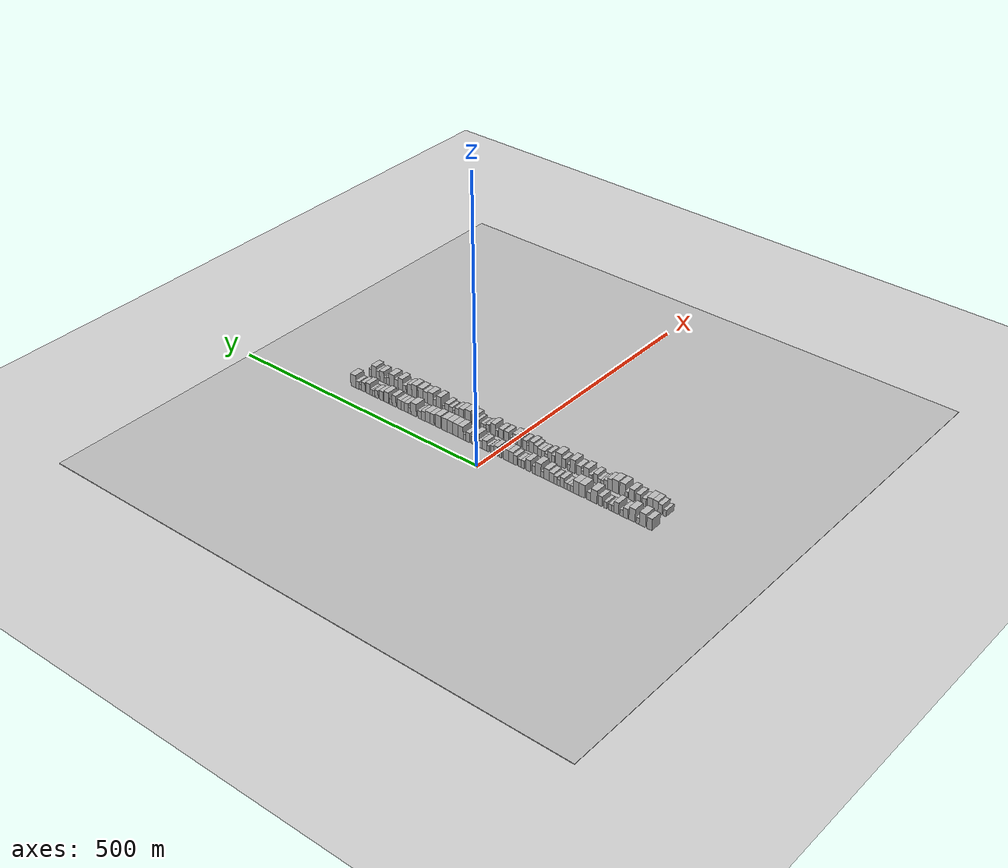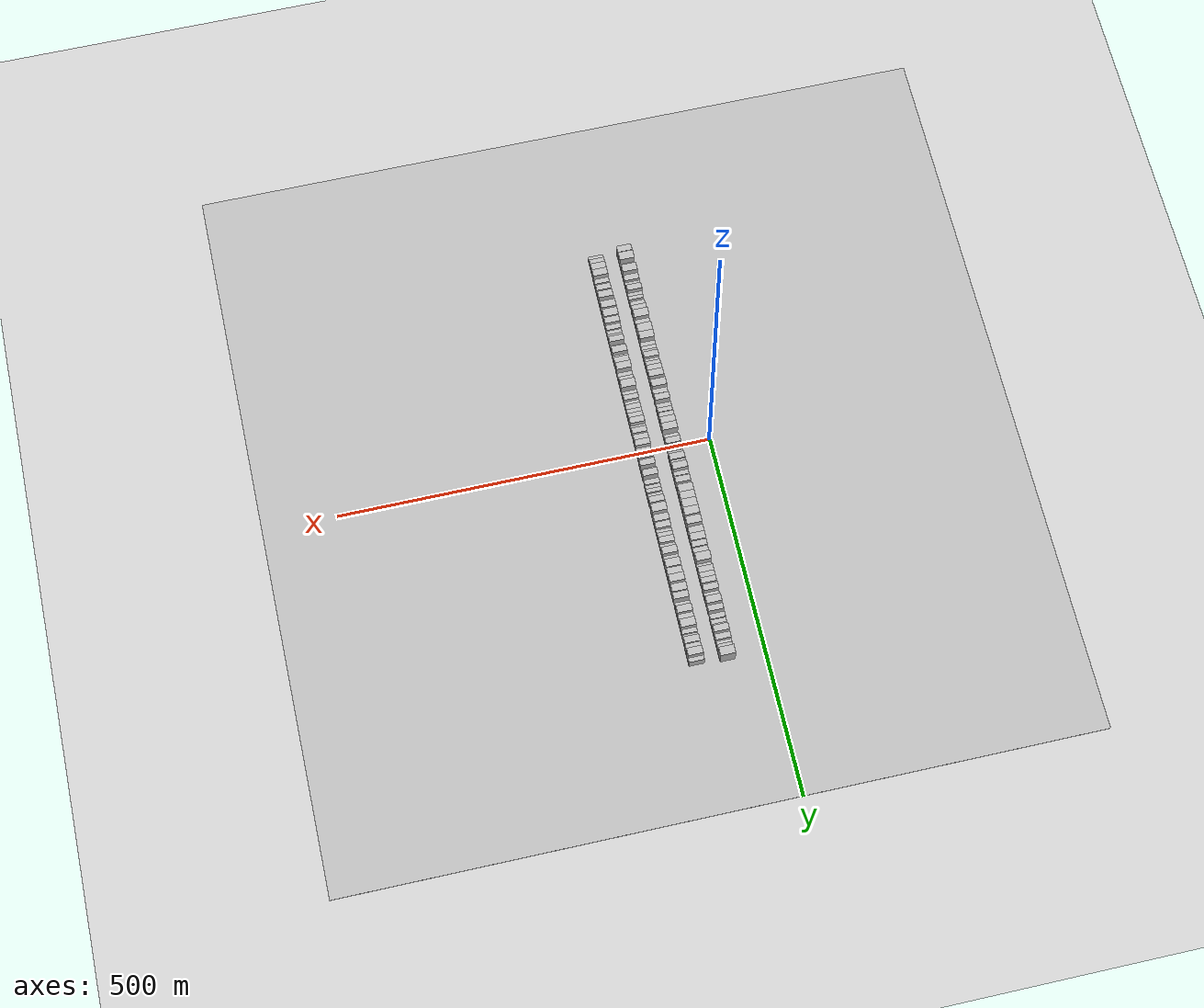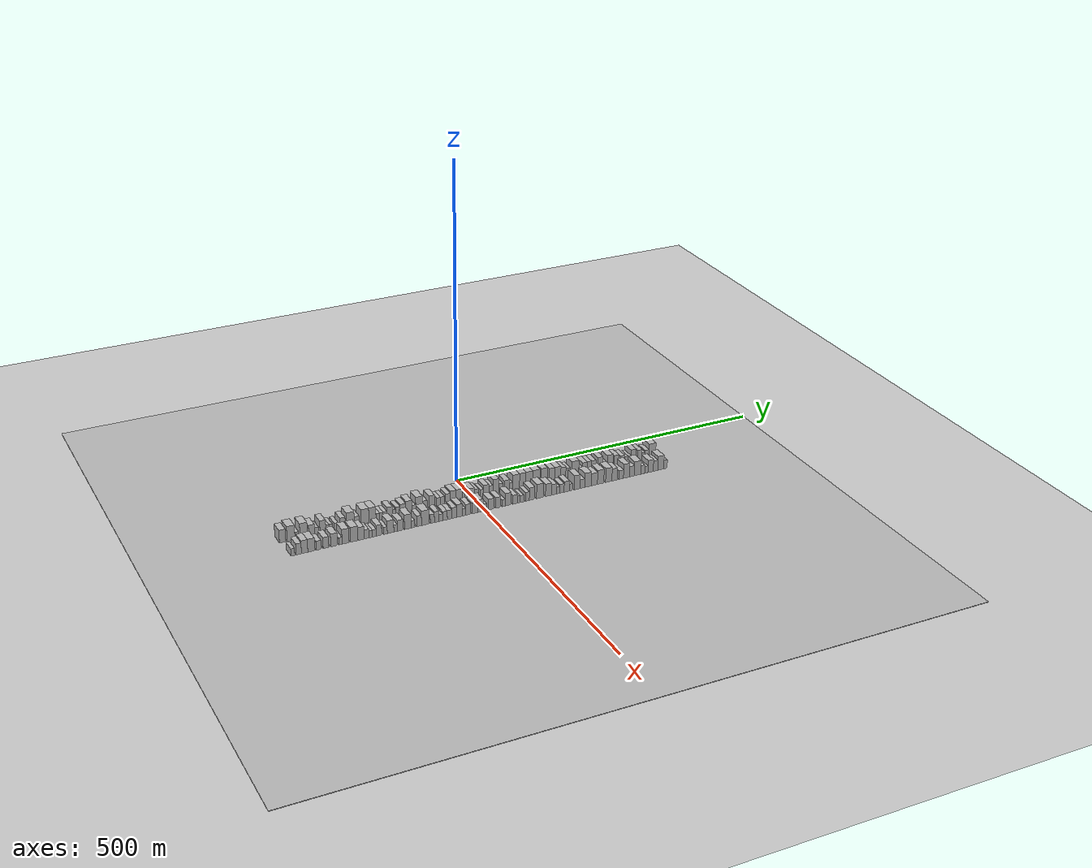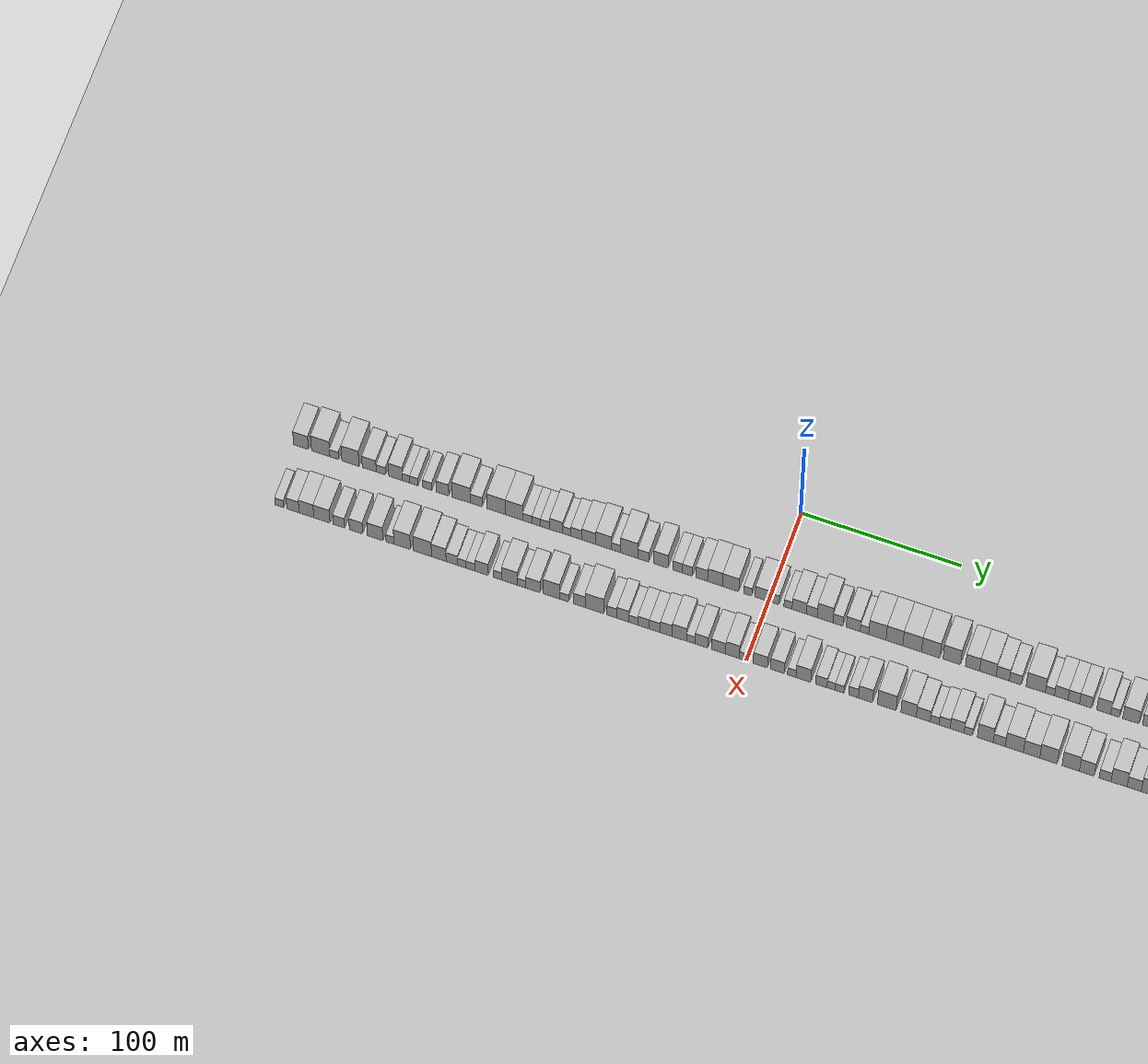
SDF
<?xml version="1.0" encoding="utf-8"?>

<sdf version="1.6">

   <world name="default">

      <gui fullscreen="0">

         <camera name="user_camera">

            <pose>-15 0 4.57585 0 0 0</pose>

            <view_controller>orbit</view_controller>

         </camera>

      </gui>

      <scene>

         <sky>

           <clouds>

             <speed>12</speed>

           </clouds>

         </sky>

         <ambient>0.4 0.4 0.4 1</ambient>

         <background>0.7 0.7 0.7 1</background>

         <shadows>1</shadows>

      </scene>

      <gravity>0 0 -9.8066</gravity>

      <magnetic_field>6e-06 2.3e-05 -4.2e-05</magnetic_field>

      <physics default="0" name="default_physics" type="ode">

         <ode>

            <solver>

               <type>quick</type>

               <iters>10</iters>

               <sor>1.0</sor>

               <use_dynamic_moi_rescaling>0</use_dynamic_moi_rescaling>

            </solver>

            <constraints>

               <cfm>0</cfm>

               <erp>0.2</erp>

               <contact_max_correcting_vel>100</contact_max_correcting_vel>

               <contact_surface_layer>0.001</contact_surface_layer>

            </constraints>

         </ode>

         <max_step_size>0.004</max_step_size>

         <real_time_factor>1</real_time_factor>

         <real_time_update_rate>250</real_time_update_rate>

      </physics>

      <light name="sun" type="directional">

         <cast_shadows>1</cast_shadows>

         <pose>0 0 10 0 0 0</pose>

         <diffuse>0.8 0.8 0.8 1</diffuse>

         <specular>0.2 0.2 0.2 1</specular>

         <attenuation>

            <range>1000</range>

            <constant>0.9</constant>

            <linear>0.01</linear>

            <quadratic>0.001</quadratic>

         </attenuation>

         <direction>-0.5 0.1 -0.9</direction>

      </light>

      <include>

         <name>ground_plane_1</name>

         <uri>model://HANNAS_ground_plane</uri>

         <pose>0 0 0  0 0 0</pose>

      </include>

      <include>

         <name>ground_plane_2</name>

         <uri>model://HANNAS_ground_plane</uri>

         <pose>100 0 0  0 0 0</pose>

      </include>

      <model name="building_1">

         <static>1</static>

         <pose frame="">50.0000 -295.3175 0 0.000000 0.000000 0.000000</pose>

         <link name="link">

            <pose frame="">0 0 10.50 0 0 0</pose>

            <collision name="collision">

               <geometry>

                  <box>

                     <size>20.0000 9.3650 21.0000</size>

                  </box>

               </geometry>

               <max_contacts>10</max_contacts>

               <surface>

                  <contact>

                     <ode/>

                  </contact>

                  <bounce/>

                  <friction>

                     <torsional>

                        <ode/>

                     </torsional>

                     <ode/>

                  </friction>

               </surface>

            </collision>

            <visual name="visual">

               <cast_shadows>0</cast_shadows>

               <geometry>

                  <box>

                     <size>20.0000 9.3650 21.0000</size>

                  </box>

               </geometry>

               <material>

                  <script>

                     <uri>model://HANNAS_wall/materials/scripts</uri>

                     <uri>model://HANNAS_wall/materials/textures</uri>

                     <name>vrc/HANNAS_wall</name>

                  </script>

               </material>

            </visual>

            <self_collide>0</self_collide>

            <enable_wind>0</enable_wind>

            <kinematic>0</kinematic>

         </link>

      </model>

      <model name="building_2">

         <static>1</static>

         <pose frame="">50.0000 -282.8107 0 0.000000 0.000000 0.000000</pose>

         <link name="link">

            <pose frame="">0 0 12.00 0 0 0</pose>

            <collision name="collision">

               <geometry>

                  <box>

                     <size>20.0000 11.6486 24.0000</size>

                  </box>

               </geometry>

               <max_contacts>10</max_contacts>

               <surface>

                  <contact>

                     <ode/>

                  </contact>

                  <bounce/>

                  <friction>

                     <torsional>

                        <ode/>

                     </torsional>

                     <ode/>

                  </friction>

               </surface>

            </collision>

            <visual name="visual">

               <cast_shadows>0</cast_shadows>

               <geometry>

                  <box>

                     <size>20.0000 11.6486 24.0000</size>

                  </box>

               </geometry>

               <material>

                  <script>

                     <uri>model://HANNAS_wall/materials/scripts</uri>

                     <uri>model://HANNAS_wall/materials/textures</uri>

                     <name>vrc/HANNAS_wall</name>

                  </script>

               </material>

            </visual>

            <self_collide>0</self_collide>

            <enable_wind>0</enable_wind>

            <kinematic>0</kinematic>

         </link>

      </model>

      <model name="building_3">

         <static>1</static>

         <pose frame="">50.0000 -274.1890 0 0.000000 0.000000 0.000000</pose>

         <link name="link">

            <pose frame="">0 0 6.00 0 0 0</pose>

            <collision name="collision">

               <geometry>

                  <box>

                     <size>20.0000 5.5949 12.0000</size>

                  </box>

               </geometry>

               <max_contacts>10</max_contacts>

               <surface>

                  <contact>

                     <ode/>

                  </contact>

                  <bounce/>

                  <friction>

                     <torsional>

                        <ode/>

                     </torsional>

                     <ode/>

                  </friction>

               </surface>

            </collision>

            <visual name="visual">

               <cast_shadows>0</cast_shadows>

               <geometry>

                  <box>

                     <size>20.0000 5.5949 12.0000</size>

                  </box>

               </geometry>

               <material>

                  <script>

                     <uri>model://HANNAS_wall/materials/scripts</uri>

                     <uri>model://HANNAS_wall/materials/textures</uri>

                     <name>vrc/HANNAS_wall</name>

                  </script>

               </material>

            </visual>

            <self_collide>0</self_collide>

            <enable_wind>0</enable_wind>

            <kinematic>0</kinematic>

         </link>

      </model>

      <model name="building_4">

         <static>1</static>

         <pose frame="">50.0000 -263.8913 0 0.000000 0.000000 0.000000</pose>

         <link name="link">

            <pose frame="">0 0 12.00 0 0 0</pose>

            <collision name="collision">

               <geometry>

                  <box>

                     <size>20.0000 11.0005 24.0000</size>

                  </box>

               </geometry>

               <max_contacts>10</max_contacts>

               <surface>

                  <contact>

                     <ode/>

                  </contact>

                  <bounce/>

                  <friction>

                     <torsional>

                        <ode/>

                     </torsional>

                     <ode/>

                  </friction>

               </surface>

            </collision>

            <visual name="visual">

               <cast_shadows>0</cast_shadows>

               <geometry>

                  <box>

                     <size>20.0000 11.0005 24.0000</size>

                  </box>

               </geometry>

               <material>

                  <script>

                     <uri>model://HANNAS_wall/materials/scripts</uri>

                     <uri>model://HANNAS_wall/materials/textures</uri>

                     <name>vrc/HANNAS_wall</name>

                  </script>

               </material>

            </visual>

            <self_collide>0</self_collide>

            <enable_wind>0</enable_wind>

            <kinematic>0</kinematic>

         </link>

      </model>

      <model name="building_5">

         <static>1</static>

         <pose frame="">50.0000 -251.9345 0 0.000000 0.000000 0.000000</pose>

         <link name="link">

            <pose frame="">0 0 9.00 0 0 0</pose>

            <collision name="collision">

               <geometry>

                  <box>

                     <size>20.0000 8.9130 18.0000</size>

                  </box>

               </geometry>

               <max_contacts>10</max_contacts>

               <surface>

                  <contact>

                     <ode/>

                  </contact>

                  <bounce/>

                  <friction>

                     <torsional>

                        <ode/>

                     </torsional>

                     <ode/>

                  </friction>

               </surface>

            </collision>

            <visual name="visual">

               <cast_shadows>0</cast_shadows>

               <geometry>

                  <box>

                     <size>20.0000 8.9130 18.0000</size>

                  </box>

               </geometry>

               <material>

                  <script>

                     <uri>model://HANNAS_wall/materials/scripts</uri>

                     <uri>model://HANNAS_wall/materials/textures</uri>

                     <name>vrc/HANNAS_wall</name>

                  </script>

               </material>

            </visual>

            <self_collide>0</self_collide>

            <enable_wind>0</enable_wind>

            <kinematic>0</kinematic>

         </link>

      </model>

      <model name="building_6">

         <static>1</static>

         <pose frame="">50.0000 -244.5130 0 0.000000 0.000000 0.000000</pose>

         <link name="link">

            <pose frame="">0 0 6.00 0 0 0</pose>

            <collision name="collision">

               <geometry>

                  <box>

                     <size>20.0000 5.9301 12.0000</size>

                  </box>

               </geometry>

               <max_contacts>10</max_contacts>

               <surface>

                  <contact>

                     <ode/>

                  </contact>

                  <bounce/>

                  <friction>

                     <torsional>

                        <ode/>

                     </torsional>

                     <ode/>

                  </friction>

               </surface>

            </collision>

            <visual name="visual">

               <cast_shadows>0</cast_shadows>

               <geometry>

                  <box>

                     <size>20.0000 5.9301 12.0000</size>

                  </box>

               </geometry>

               <material>

                  <script>

                     <uri>model://HANNAS_wall/materials/scripts</uri>

                     <uri>model://HANNAS_wall/materials/textures</uri>

                     <name>vrc/HANNAS_wall</name>

                  </script>

               </material>

            </visual>

            <self_collide>0</self_collide>

            <enable_wind>0</enable_wind>

            <kinematic>0</kinematic>

         </link>

      </model>

      <model name="building_7">

         <static>1</static>

         <pose frame="">50.0000 -235.2398 0 0.000000 0.000000 0.000000</pose>

         <link name="link">

            <pose frame="">0 0 10.50 0 0 0</pose>

            <collision name="collision">

               <geometry>

                  <box>

                     <size>20.0000 8.6164 21.0000</size>

                  </box>

               </geometry>

               <max_contacts>10</max_contacts>

               <surface>

                  <contact>

                     <ode/>

                  </contact>

                  <bounce/>

                  <friction>

                     <torsional>

                        <ode/>

                     </torsional>

                     <ode/>

                  </friction>

               </surface>

            </collision>

            <visual name="visual">

               <cast_shadows>0</cast_shadows>

               <geometry>

                  <box>

                     <size>20.0000 8.6164 21.0000</size>

                  </box>

               </geometry>

               <material>

                  <script>

                     <uri>model://HANNAS_wall/materials/scripts</uri>

                     <uri>model://HANNAS_wall/materials/textures</uri>

                     <name>vrc/HANNAS_wall</name>

                  </script>

               </material>

            </visual>

            <self_collide>0</self_collide>

            <enable_wind>0</enable_wind>

            <kinematic>0</kinematic>

         </link>

      </model>

      <model name="building_8">

         <static>1</static>

         <pose frame="">50.0000 -228.5288 0 0.000000 0.000000 0.000000</pose>

         <link name="link">

            <pose frame="">0 0 6.00 0 0 0</pose>

            <collision name="collision">

               <geometry>

                  <box>

                     <size>20.0000 4.8055 12.0000</size>

                  </box>

               </geometry>

               <max_contacts>10</max_contacts>

               <surface>

                  <contact>

                     <ode/>

                  </contact>

                  <bounce/>

                  <friction>

                     <torsional>

                        <ode/>

                     </torsional>

                     <ode/>

                  </friction>

               </surface>

            </collision>

            <visual name="visual">

               <cast_shadows>0</cast_shadows>

               <geometry>

                  <box>

                     <size>20.0000 4.8055 12.0000</size>

                  </box>

               </geometry>

               <material>

                  <script>

                     <uri>model://HANNAS_wall/materials/scripts</uri>

                     <uri>model://HANNAS_wall/materials/textures</uri>

                     <name>vrc/HANNAS_wall</name>

                  </script>

               </material>

            </visual>

            <self_collide>0</self_collide>

            <enable_wind>0</enable_wind>

            <kinematic>0</kinematic>

         </link>

      </model>

      <model name="building_9">

         <static>1</static>

         <pose frame="">50.0000 -223.5332 0 0.000000 0.000000 0.000000</pose>

         <link name="link">

            <pose frame="">0 0 6.00 0 0 0</pose>

            <collision name="collision">

               <geometry>

                  <box>

                     <size>20.0000 5.1856 12.0000</size>

                  </box>

               </geometry>

               <max_contacts>10</max_contacts>

               <surface>

                  <contact>

                     <ode/>

                  </contact>

                  <bounce/>

                  <friction>

                     <torsional>

                        <ode/>

                     </torsional>

                     <ode/>

                  </friction>

               </surface>

            </collision>

            <visual name="visual">

               <cast_shadows>0</cast_shadows>

               <geometry>

                  <box>

                     <size>20.0000 5.1856 12.0000</size>

                  </box>

               </geometry>

               <material>

                  <script>

                     <uri>model://HANNAS_wall/materials/scripts</uri>

                     <uri>model://HANNAS_wall/materials/textures</uri>

                     <name>vrc/HANNAS_wall</name>

                  </script>

               </material>

            </visual>

            <self_collide>0</self_collide>

            <enable_wind>0</enable_wind>

            <kinematic>0</kinematic>

         </link>

      </model>

      <model name="building_10">

         <static>1</static>

         <pose frame="">50.0000 -215.0682 0 0.000000 0.000000 0.000000</pose>

         <link name="link">

            <pose frame="">0 0 6.00 0 0 0</pose>

            <collision name="collision">

               <geometry>

                  <box>

                     <size>20.0000 5.7443 12.0000</size>

                  </box>

               </geometry>

               <max_contacts>10</max_contacts>

               <surface>

                  <contact>

                     <ode/>

                  </contact>

                  <bounce/>

                  <friction>

                     <torsional>

                        <ode/>

                     </torsional>

                     <ode/>

                  </friction>

               </surface>

            </collision>

            <visual name="visual">

               <cast_shadows>0</cast_shadows>

               <geometry>

                  <box>

                     <size>20.0000 5.7443 12.0000</size>

                  </box>

               </geometry>

               <material>

                  <script>

                     <uri>model://HANNAS_wall/materials/scripts</uri>

                     <uri>model://HANNAS_wall/materials/textures</uri>

                     <name>vrc/HANNAS_wall</name>

                  </script>

               </material>

            </visual>

            <self_collide>0</self_collide>

            <enable_wind>0</enable_wind>

            <kinematic>0</kinematic>

         </link>

      </model>

      <model name="building_11">

         <static>1</static>

         <pose frame="">50.0000 -205.3281 0 0.000000 0.000000 0.000000</pose>

         <link name="link">

            <pose frame="">0 0 9.00 0 0 0</pose>

            <collision name="collision">

               <geometry>

                  <box>

                     <size>20.0000 7.7359 18.0000</size>

                  </box>

               </geometry>

               <max_contacts>10</max_contacts>

               <surface>

                  <contact>

                     <ode/>

                  </contact>

                  <bounce/>

                  <friction>

                     <torsional>

                        <ode/>

                     </torsional>

                     <ode/>

                  </friction>

               </surface>

            </collision>

            <visual name="visual">

               <cast_shadows>0</cast_shadows>

               <geometry>

                  <box>

                     <size>20.0000 7.7359 18.0000</size>

                  </box>

               </geometry>

               <material>

                  <script>

                     <uri>model://HANNAS_wall/materials/scripts</uri>

                     <uri>model://HANNAS_wall/materials/textures</uri>

                     <name>vrc/HANNAS_wall</name>

                  </script>

               </material>

            </visual>

            <self_collide>0</self_collide>

            <enable_wind>0</enable_wind>

            <kinematic>0</kinematic>

         </link>

      </model>

      <model name="building_12">

         <static>1</static>

         <pose frame="">50.0000 -193.6278 0 0.000000 0.000000 0.000000</pose>

         <link name="link">

            <pose frame="">0 0 12.00 0 0 0</pose>

            <collision name="collision">

               <geometry>

                  <box>

                     <size>20.0000 11.6648 24.0000</size>

                  </box>

               </geometry>

               <max_contacts>10</max_contacts>

               <surface>

                  <contact>

                     <ode/>

                  </contact>

                  <bounce/>

                  <friction>

                     <torsional>

                        <ode/>

                     </torsional>

                     <ode/>

                  </friction>

               </surface>

            </collision>

            <visual name="visual">

               <cast_shadows>0</cast_shadows>

               <geometry>

                  <box>

                     <size>20.0000 11.6648 24.0000</size>

                  </box>

               </geometry>

               <material>

                  <script>

                     <uri>model://HANNAS_wall/materials/scripts</uri>

                     <uri>model://HANNAS_wall/materials/textures</uri>

                     <name>vrc/HANNAS_wall</name>

                  </script>

               </material>

            </visual>

            <self_collide>0</self_collide>

            <enable_wind>0</enable_wind>

            <kinematic>0</kinematic>

         </link>

      </model>

      <model name="building_13">

         <static>1</static>

         <pose frame="">50.0000 -184.0830 0 0.000000 0.000000 0.000000</pose>

         <link name="link">

            <pose frame="">0 0 7.50 0 0 0</pose>

            <collision name="collision">

               <geometry>

                  <box>

                     <size>20.0000 7.4248 15.0000</size>

                  </box>

               </geometry>

               <max_contacts>10</max_contacts>

               <surface>

                  <contact>

                     <ode/>

                  </contact>

                  <bounce/>

                  <friction>

                     <torsional>

                        <ode/>

                     </torsional>

                     <ode/>

                  </friction>

               </surface>

            </collision>

            <visual name="visual">

               <cast_shadows>0</cast_shadows>

               <geometry>

                  <box>

                     <size>20.0000 7.4248 15.0000</size>

                  </box>

               </geometry>

               <material>

                  <script>

                     <uri>model://HANNAS_wall/materials/scripts</uri>

                     <uri>model://HANNAS_wall/materials/textures</uri>

                     <name>vrc/HANNAS_wall</name>

                  </script>

               </material>

            </visual>

            <self_collide>0</self_collide>

            <enable_wind>0</enable_wind>

            <kinematic>0</kinematic>

         </link>

      </model>

      <model name="building_14">

         <static>1</static>

         <pose frame="">50.0000 -171.4516 0 0.000000 0.000000 0.000000</pose>

         <link name="link">

            <pose frame="">0 0 12.00 0 0 0</pose>

            <collision name="collision">

               <geometry>

                  <box>

                     <size>20.0000 11.8380 24.0000</size>

                  </box>

               </geometry>

               <max_contacts>10</max_contacts>

               <surface>

                  <contact>

                     <ode/>

                  </contact>

                  <bounce/>

                  <friction>

                     <torsional>

                        <ode/>

                     </torsional>

                     <ode/>

                  </friction>

               </surface>

            </collision>

            <visual name="visual">

               <cast_shadows>0</cast_shadows>

               <geometry>

                  <box>

                     <size>20.0000 11.8380 24.0000</size>

                  </box>

               </geometry>

               <material>

                  <script>

                     <uri>model://HANNAS_wall/materials/scripts</uri>

                     <uri>model://HANNAS_wall/materials/textures</uri>

                     <name>vrc/HANNAS_wall</name>

                  </script>

               </material>

            </visual>

            <self_collide>0</self_collide>

            <enable_wind>0</enable_wind>

            <kinematic>0</kinematic>

         </link>

      </model>

      <model name="building_15">

         <static>1</static>

         <pose frame="">50.0000 -160.0924 0 0.000000 0.000000 0.000000</pose>

         <link name="link">

            <pose frame="">0 0 12.00 0 0 0</pose>

            <collision name="collision">

               <geometry>

                  <box>

                     <size>20.0000 10.8804 24.0000</size>

                  </box>

               </geometry>

               <max_contacts>10</max_contacts>

               <surface>

                  <contact>

                     <ode/>

                  </contact>

                  <bounce/>

                  <friction>

                     <torsional>

                        <ode/>

                     </torsional>

                     <ode/>

                  </friction>

               </surface>

            </collision>

            <visual name="visual">

               <cast_shadows>0</cast_shadows>

               <geometry>

                  <box>

                     <size>20.0000 10.8804 24.0000</size>

                  </box>

               </geometry>

               <material>

                  <script>

                     <uri>model://HANNAS_wall/materials/scripts</uri>

                     <uri>model://HANNAS_wall/materials/textures</uri>

                     <name>vrc/HANNAS_wall</name>

                  </script>

               </material>

            </visual>

            <self_collide>0</self_collide>

            <enable_wind>0</enable_wind>

            <kinematic>0</kinematic>

         </link>

      </model>

      <model name="building_16">

         <static>1</static>

         <pose frame="">50.0000 -151.7578 0 0.000000 0.000000 0.000000</pose>

         <link name="link">

            <pose frame="">0 0 6.00 0 0 0</pose>

            <collision name="collision">

               <geometry>

                  <box>

                     <size>20.0000 5.7887 12.0000</size>

                  </box>

               </geometry>

               <max_contacts>10</max_contacts>

               <surface>

                  <contact>

                     <ode/>

                  </contact>

                  <bounce/>

                  <friction>

                     <torsional>

                        <ode/>

                     </torsional>

                     <ode/>

                  </friction>

               </surface>

            </collision>

            <visual name="visual">

               <cast_shadows>0</cast_shadows>

               <geometry>

                  <box>

                     <size>20.0000 5.7887 12.0000</size>

                  </box>

               </geometry>

               <material>

                  <script>

                     <uri>model://HANNAS_wall/materials/scripts</uri>

                     <uri>model://HANNAS_wall/materials/textures</uri>

                     <name>vrc/HANNAS_wall</name>

                  </script>

               </material>

            </visual>

            <self_collide>0</self_collide>

            <enable_wind>0</enable_wind>

            <kinematic>0</kinematic>

         </link>

      </model>

      <model name="building_17">

         <static>1</static>

         <pose frame="">50.0000 -146.1758 0 0.000000 0.000000 0.000000</pose>

         <link name="link">

            <pose frame="">0 0 6.00 0 0 0</pose>

            <collision name="collision">

               <geometry>

                  <box>

                     <size>20.0000 5.3753 12.0000</size>

                  </box>

               </geometry>

               <max_contacts>10</max_contacts>

               <surface>

                  <contact>

                     <ode/>

                  </contact>

                  <bounce/>

                  <friction>

                     <torsional>

                        <ode/>

                     </torsional>

                     <ode/>

                  </friction>

               </surface>

            </collision>

            <visual name="visual">

               <cast_shadows>0</cast_shadows>

               <geometry>

                  <box>

                     <size>20.0000 5.3753 12.0000</size>

                  </box>

               </geometry>

               <material>

                  <script>

                     <uri>model://HANNAS_wall/materials/scripts</uri>

                     <uri>model://HANNAS_wall/materials/textures</uri>

                     <name>vrc/HANNAS_wall</name>

                  </script>

               </material>

            </visual>

            <self_collide>0</self_collide>

            <enable_wind>0</enable_wind>

            <kinematic>0</kinematic>

         </link>

      </model>

      <model name="building_18">

         <static>1</static>

         <pose frame="">50.0000 -140.6003 0 0.000000 0.000000 0.000000</pose>

         <link name="link">

            <pose frame="">0 0 6.00 0 0 0</pose>

            <collision name="collision">

               <geometry>

                  <box>

                     <size>20.0000 5.7758 12.0000</size>

                  </box>

               </geometry>

               <max_contacts>10</max_contacts>

               <surface>

                  <contact>

                     <ode/>

                  </contact>

                  <bounce/>

                  <friction>

                     <torsional>

                        <ode/>

                     </torsional>

                     <ode/>

                  </friction>

               </surface>

            </collision>

            <visual name="visual">

               <cast_shadows>0</cast_shadows>

               <geometry>

                  <box>

                     <size>20.0000 5.7758 12.0000</size>

                  </box>

               </geometry>

               <material>

                  <script>

                     <uri>model://HANNAS_wall/materials/scripts</uri>

                     <uri>model://HANNAS_wall/materials/textures</uri>

                     <name>vrc/HANNAS_wall</name>

                  </script>

               </material>

            </visual>

            <self_collide>0</self_collide>

            <enable_wind>0</enable_wind>

            <kinematic>0</kinematic>

         </link>

      </model>

      <model name="building_19">

         <static>1</static>

         <pose frame="">50.0000 -133.5268 0 0.000000 0.000000 0.000000</pose>

         <link name="link">

            <pose frame="">0 0 9.00 0 0 0</pose>

            <collision name="collision">

               <geometry>

                  <box>

                     <size>20.0000 8.3712 18.0000</size>

                  </box>

               </geometry>

               <max_contacts>10</max_contacts>

               <surface>

                  <contact>

                     <ode/>

                  </contact>

                  <bounce/>

                  <friction>

                     <torsional>

                        <ode/>

                     </torsional>

                     <ode/>

                  </friction>

               </surface>

            </collision>

            <visual name="visual">

               <cast_shadows>0</cast_shadows>

               <geometry>

                  <box>

                     <size>20.0000 8.3712 18.0000</size>

                  </box>

               </geometry>

               <material>

                  <script>

                     <uri>model://HANNAS_wall/materials/scripts</uri>

                     <uri>model://HANNAS_wall/materials/textures</uri>

                     <name>vrc/HANNAS_wall</name>

                  </script>

               </material>

            </visual>

            <self_collide>0</self_collide>

            <enable_wind>0</enable_wind>

            <kinematic>0</kinematic>

         </link>

      </model>

      <model name="building_20">

         <static>1</static>

         <pose frame="">50.0000 -126.8570 0 0.000000 0.000000 0.000000</pose>

         <link name="link">

            <pose frame="">0 0 6.00 0 0 0</pose>

            <collision name="collision">

               <geometry>

                  <box>

                     <size>20.0000 4.9683 12.0000</size>

                  </box>

               </geometry>

               <max_contacts>10</max_contacts>

               <surface>

                  <contact>

                     <ode/>

                  </contact>

                  <bounce/>

                  <friction>

                     <torsional>

                        <ode/>

                     </torsional>

                     <ode/>

                  </friction>

               </surface>

            </collision>

            <visual name="visual">

               <cast_shadows>0</cast_shadows>

               <geometry>

                  <box>

                     <size>20.0000 4.9683 12.0000</size>

                  </box>

               </geometry>

               <material>

                  <script>

                     <uri>model://HANNAS_wall/materials/scripts</uri>

                     <uri>model://HANNAS_wall/materials/textures</uri>

                     <name>vrc/HANNAS_wall</name>

                  </script>

               </material>

            </visual>

            <self_collide>0</self_collide>

            <enable_wind>0</enable_wind>

            <kinematic>0</kinematic>

         </link>

      </model>

      <model name="building_21">

         <static>1</static>

         <pose frame="">50.0000 -120.8502 0 0.000000 0.000000 0.000000</pose>

         <link name="link">

            <pose frame="">0 0 7.50 0 0 0</pose>

            <collision name="collision">

               <geometry>

                  <box>

                     <size>20.0000 7.0453 15.0000</size>

                  </box>

               </geometry>

               <max_contacts>10</max_contacts>

               <surface>

                  <contact>

                     <ode/>

                  </contact>

                  <bounce/>

                  <friction>

                     <torsional>

                        <ode/>

                     </torsional>

                     <ode/>

                  </friction>

               </surface>

            </collision>

            <visual name="visual">

               <cast_shadows>0</cast_shadows>

               <geometry>

                  <box>

                     <size>20.0000 7.0453 15.0000</size>

                  </box>

               </geometry>

               <material>

                  <script>

                     <uri>model://HANNAS_wall/materials/scripts</uri>

                     <uri>model://HANNAS_wall/materials/textures</uri>

                     <name>vrc/HANNAS_wall</name>

                  </script>

               </material>

            </visual>

            <self_collide>0</self_collide>

            <enable_wind>0</enable_wind>

            <kinematic>0</kinematic>

         </link>

      </model>

      <model name="building_22">

         <static>1</static>

         <pose frame="">50.0000 -112.8907 0 0.000000 0.000000 0.000000</pose>

         <link name="link">

            <pose frame="">0 0 9.00 0 0 0</pose>

            <collision name="collision">

               <geometry>

                  <box>

                     <size>20.0000 8.8738 18.0000</size>

                  </box>

               </geometry>

               <max_contacts>10</max_contacts>

               <surface>

                  <contact>

                     <ode/>

                  </contact>

                  <bounce/>

                  <friction>

                     <torsional>

                        <ode/>

                     </torsional>

                     <ode/>

                  </friction>

               </surface>

            </collision>

            <visual name="visual">

               <cast_shadows>0</cast_shadows>

               <geometry>

                  <box>

                     <size>20.0000 8.8738 18.0000</size>

                  </box>

               </geometry>

               <material>

                  <script>

                     <uri>model://HANNAS_wall/materials/scripts</uri>

                     <uri>model://HANNAS_wall/materials/textures</uri>

                     <name>vrc/HANNAS_wall</name>

                  </script>

               </material>

            </visual>

            <self_collide>0</self_collide>

            <enable_wind>0</enable_wind>

            <kinematic>0</kinematic>

         </link>

      </model>

      <model name="building_23">

         <static>1</static>

         <pose frame="">50.0000 -103.5695 0 0.000000 0.000000 0.000000</pose>

         <link name="link">

            <pose frame="">0 0 10.50 0 0 0</pose>

            <collision name="collision">

               <geometry>

                  <box>

                     <size>20.0000 9.7686 21.0000</size>

                  </box>

               </geometry>

               <max_contacts>10</max_contacts>

               <surface>

                  <contact>

                     <ode/>

                  </contact>

                  <bounce/>

                  <friction>

                     <torsional>

                        <ode/>

                     </torsional>

                     <ode/>

                  </friction>

               </surface>

            </collision>

            <visual name="visual">

               <cast_shadows>0</cast_shadows>

               <geometry>

                  <box>

                     <size>20.0000 9.7686 21.0000</size>

                  </box>

               </geometry>

               <material>

                  <script>

                     <uri>model://HANNAS_wall/materials/scripts</uri>

                     <uri>model://HANNAS_wall/materials/textures</uri>

                     <name>vrc/HANNAS_wall</name>

                  </script>

               </material>

            </visual>

            <self_collide>0</self_collide>

            <enable_wind>0</enable_wind>

            <kinematic>0</kinematic>

         </link>

      </model>

      <model name="building_24">

         <static>1</static>

         <pose frame="">50.0000 -95.7986 0 0.000000 0.000000 0.000000</pose>

         <link name="link">

            <pose frame="">0 0 6.00 0 0 0</pose>

            <collision name="collision">

               <geometry>

                  <box>

                     <size>20.0000 5.7732 12.0000</size>

                  </box>

               </geometry>

               <max_contacts>10</max_contacts>

               <surface>

                  <contact>

                     <ode/>

                  </contact>

                  <bounce/>

                  <friction>

                     <torsional>

                        <ode/>

                     </torsional>

                     <ode/>

                  </friction>

               </surface>

            </collision>

            <visual name="visual">

               <cast_shadows>0</cast_shadows>

               <geometry>

                  <box>

                     <size>20.0000 5.7732 12.0000</size>

                  </box>

               </geometry>

               <material>

                  <script>

                     <uri>model://HANNAS_wall/materials/scripts</uri>

                     <uri>model://HANNAS_wall/materials/textures</uri>

                     <name>vrc/HANNAS_wall</name>

                  </script>

               </material>

            </visual>

            <self_collide>0</self_collide>

            <enable_wind>0</enable_wind>

            <kinematic>0</kinematic>

         </link>

      </model>

      <model name="building_25">

         <static>1</static>

         <pose frame="">50.0000 -87.5383 0 0.000000 0.000000 0.000000</pose>

         <link name="link">

            <pose frame="">0 0 12.00 0 0 0</pose>

            <collision name="collision">

               <geometry>

                  <box>

                     <size>20.0000 10.7474 24.0000</size>

                  </box>

               </geometry>

               <max_contacts>10</max_contacts>

               <surface>

                  <contact>

                     <ode/>

                  </contact>

                  <bounce/>

                  <friction>

                     <torsional>

                        <ode/>

                     </torsional>

                     <ode/>

                  </friction>

               </surface>

            </collision>

            <visual name="visual">

               <cast_shadows>0</cast_shadows>

               <geometry>

                  <box>

                     <size>20.0000 10.7474 24.0000</size>

                  </box>

               </geometry>

               <material>

                  <script>

                     <uri>model://HANNAS_wall/materials/scripts</uri>

                     <uri>model://HANNAS_wall/materials/textures</uri>

                     <name>vrc/HANNAS_wall</name>

                  </script>

               </material>

            </visual>

            <self_collide>0</self_collide>

            <enable_wind>0</enable_wind>

            <kinematic>0</kinematic>

         </link>

      </model>

      <model name="building_26">

         <static>1</static>

         <pose frame="">50.0000 -78.6126 0 0.000000 0.000000 0.000000</pose>

         <link name="link">

            <pose frame="">0 0 7.50 0 0 0</pose>

            <collision name="collision">

               <geometry>

                  <box>

                     <size>20.0000 7.1039 15.0000</size>

                  </box>

               </geometry>

               <max_contacts>10</max_contacts>

               <surface>

                  <contact>

                     <ode/>

                  </contact>

                  <bounce/>

                  <friction>

                     <torsional>

                        <ode/>

                     </torsional>

                     <ode/>

                  </friction>

               </surface>

            </collision>

            <visual name="visual">

               <cast_shadows>0</cast_shadows>

               <geometry>

                  <box>

                     <size>20.0000 7.1039 15.0000</size>

                  </box>

               </geometry>

               <material>

                  <script>

                     <uri>model://HANNAS_wall/materials/scripts</uri>

                     <uri>model://HANNAS_wall/materials/textures</uri>

                     <name>vrc/HANNAS_wall</name>

                  </script>

               </material>

            </visual>

            <self_collide>0</self_collide>

            <enable_wind>0</enable_wind>

            <kinematic>0</kinematic>

         </link>

      </model>

      <model name="building_27">

         <static>1</static>

         <pose frame="">50.0000 -67.5679 0 0.000000 0.000000 0.000000</pose>

         <link name="link">

            <pose frame="">0 0 10.50 0 0 0</pose>

            <collision name="collision">

               <geometry>

                  <box>

                     <size>20.0000 8.9856 21.0000</size>

                  </box>

               </geometry>

               <max_contacts>10</max_contacts>

               <surface>

                  <contact>

                     <ode/>

                  </contact>

                  <bounce/>

                  <friction>

                     <torsional>

                        <ode/>

                     </torsional>

                     <ode/>

                  </friction>

               </surface>

            </collision>

            <visual name="visual">

               <cast_shadows>0</cast_shadows>

               <geometry>

                  <box>

                     <size>20.0000 8.9856 21.0000</size>

                  </box>

               </geometry>

               <material>

                  <script>

                     <uri>model://HANNAS_wall/materials/scripts</uri>

                     <uri>model://HANNAS_wall/materials/textures</uri>

                     <name>vrc/HANNAS_wall</name>

                  </script>

               </material>

            </visual>

            <self_collide>0</self_collide>

            <enable_wind>0</enable_wind>

            <kinematic>0</kinematic>

         </link>

      </model>

      <model name="building_28">

         <static>1</static>

         <pose frame="">50.0000 -57.0685 0 0.000000 0.000000 0.000000</pose>

         <link name="link">

            <pose frame="">0 0 7.50 0 0 0</pose>

            <collision name="collision">

               <geometry>

                  <box>

                     <size>20.0000 6.0131 15.0000</size>

                  </box>

               </geometry>

               <max_contacts>10</max_contacts>

               <surface>

                  <contact>

                     <ode/>

                  </contact>

                  <bounce/>

                  <friction>

                     <torsional>

                        <ode/>

                     </torsional>

                     <ode/>

                  </friction>

               </surface>

            </collision>

            <visual name="visual">

               <cast_shadows>0</cast_shadows>

               <geometry>

                  <box>

                     <size>20.0000 6.0131 15.0000</size>

                  </box>

               </geometry>

               <material>

                  <script>

                     <uri>model://HANNAS_wall/materials/scripts</uri>

                     <uri>model://HANNAS_wall/materials/textures</uri>

                     <name>vrc/HANNAS_wall</name>

                  </script>

               </material>

            </visual>

            <self_collide>0</self_collide>

            <enable_wind>0</enable_wind>

            <kinematic>0</kinematic>

         </link>

      </model>

      <model name="building_29">

         <static>1</static>

         <pose frame="">50.0000 -50.8885 0 0.000000 0.000000 0.000000</pose>

         <link name="link">

            <pose frame="">0 0 7.50 0 0 0</pose>

            <collision name="collision">

               <geometry>

                  <box>

                     <size>20.0000 6.3470 15.0000</size>

                  </box>

               </geometry>

               <max_contacts>10</max_contacts>

               <surface>

                  <contact>

                     <ode/>

                  </contact>

                  <bounce/>

                  <friction>

                     <torsional>

                        <ode/>

                     </torsional>

                     <ode/>

                  </friction>

               </surface>

            </collision>

            <visual name="visual">

               <cast_shadows>0</cast_shadows>

               <geometry>

                  <box>

                     <size>20.0000 6.3470 15.0000</size>

                  </box>

               </geometry>

               <material>

                  <script>

                     <uri>model://HANNAS_wall/materials/scripts</uri>

                     <uri>model://HANNAS_wall/materials/textures</uri>

                     <name>vrc/HANNAS_wall</name>

                  </script>

               </material>

            </visual>

            <self_collide>0</self_collide>

            <enable_wind>0</enable_wind>

            <kinematic>0</kinematic>

         </link>

      </model>

      <model name="building_30">

         <static>1</static>

         <pose frame="">50.0000 -41.9861 0 0.000000 0.000000 0.000000</pose>

         <link name="link">

            <pose frame="">0 0 9.00 0 0 0</pose>

            <collision name="collision">

               <geometry>

                  <box>

                     <size>20.0000 7.4578 18.0000</size>

                  </box>

               </geometry>

               <max_contacts>10</max_contacts>

               <surface>

                  <contact>

                     <ode/>

                  </contact>

                  <bounce/>

                  <friction>

                     <torsional>

                        <ode/>

                     </torsional>

                     <ode/>

                  </friction>

               </surface>

            </collision>

            <visual name="visual">

               <cast_shadows>0</cast_shadows>

               <geometry>

                  <box>

                     <size>20.0000 7.4578 18.0000</size>

                  </box>

               </geometry>

               <material>

                  <script>

                     <uri>model://HANNAS_wall/materials/scripts</uri>

                     <uri>model://HANNAS_wall/materials/textures</uri>

                     <name>vrc/HANNAS_wall</name>

                  </script>

               </material>

            </visual>

            <self_collide>0</self_collide>

            <enable_wind>0</enable_wind>

            <kinematic>0</kinematic>

         </link>

      </model>

      <model name="building_31">

         <static>1</static>

         <pose frame="">50.0000 -33.5933 0 0.000000 0.000000 0.000000</pose>

         <link name="link">

            <pose frame="">0 0 10.50 0 0 0</pose>

            <collision name="collision">

               <geometry>

                  <box>

                     <size>20.0000 9.3279 21.0000</size>

                  </box>

               </geometry>

               <max_contacts>10</max_contacts>

               <surface>

                  <contact>

                     <ode/>

                  </contact>

                  <bounce/>

                  <friction>

                     <torsional>

                        <ode/>

                     </torsional>

                     <ode/>

                  </friction>

               </surface>

            </collision>

            <visual name="visual">

               <cast_shadows>0</cast_shadows>

               <geometry>

                  <box>

                     <size>20.0000 9.3279 21.0000</size>

                  </box>

               </geometry>

               <material>

                  <script>

                     <uri>model://HANNAS_wall/materials/scripts</uri>

                     <uri>model://HANNAS_wall/materials/textures</uri>

                     <name>vrc/HANNAS_wall</name>

                  </script>

               </material>

            </visual>

            <self_collide>0</self_collide>

            <enable_wind>0</enable_wind>

            <kinematic>0</kinematic>

         </link>

      </model>

      <model name="building_32">

         <static>1</static>

         <pose frame="">50.0000 -23.7865 0 0.000000 0.000000 0.000000</pose>

         <link name="link">

            <pose frame="">0 0 10.50 0 0 0</pose>

            <collision name="collision">

               <geometry>

                  <box>

                     <size>20.0000 10.2857 21.0000</size>

                  </box>

               </geometry>

               <max_contacts>10</max_contacts>

               <surface>

                  <contact>

                     <ode/>

                  </contact>

                  <bounce/>

                  <friction>

                     <torsional>

                        <ode/>

                     </torsional>

                     <ode/>

                  </friction>

               </surface>

            </collision>

            <visual name="visual">

               <cast_shadows>0</cast_shadows>

               <geometry>

                  <box>

                     <size>20.0000 10.2857 21.0000</size>

                  </box>

               </geometry>

               <material>

                  <script>

                     <uri>model://HANNAS_wall/materials/scripts</uri>

                     <uri>model://HANNAS_wall/materials/textures</uri>

                     <name>vrc/HANNAS_wall</name>

                  </script>

               </material>

            </visual>

            <self_collide>0</self_collide>

            <enable_wind>0</enable_wind>

            <kinematic>0</kinematic>

         </link>

      </model>

      <model name="building_33">

         <static>1</static>

         <pose frame="">50.0000 -13.0210 0 0.000000 0.000000 0.000000</pose>

         <link name="link">

            <pose frame="">0 0 6.00 0 0 0</pose>

            <collision name="collision">

               <geometry>

                  <box>

                     <size>20.0000 5.2452 12.0000</size>

                  </box>

               </geometry>

               <max_contacts>10</max_contacts>

               <surface>

                  <contact>

                     <ode/>

                  </contact>

                  <bounce/>

                  <friction>

                     <torsional>

                        <ode/>

                     </torsional>

                     <ode/>

                  </friction>

               </surface>

            </collision>

            <visual name="visual">

               <cast_shadows>0</cast_shadows>

               <geometry>

                  <box>

                     <size>20.0000 5.2452 12.0000</size>

                  </box>

               </geometry>

               <material>

                  <script>

                     <uri>model://HANNAS_wall/materials/scripts</uri>

                     <uri>model://HANNAS_wall/materials/textures</uri>

                     <name>vrc/HANNAS_wall</name>

                  </script>

               </material>

            </visual>

            <self_collide>0</self_collide>

            <enable_wind>0</enable_wind>

            <kinematic>0</kinematic>

         </link>

      </model>

      <model name="building_34">

         <static>1</static>

         <pose frame="">50.0000 -4.1912 0 0.000000 0.000000 0.000000</pose>

         <link name="link">

            <pose frame="">0 0 9.00 0 0 0</pose>

            <collision name="collision">

               <geometry>

                  <box>

                     <size>20.0000 8.4145 18.0000</size>

                  </box>

               </geometry>

               <max_contacts>10</max_contacts>

               <surface>

                  <contact>

                     <ode/>

                  </contact>

                  <bounce/>

                  <friction>

                     <torsional>

                        <ode/>

                     </torsional>

                     <ode/>

                  </friction>

               </surface>

            </collision>

            <visual name="visual">

               <cast_shadows>0</cast_shadows>

               <geometry>

                  <box>

                     <size>20.0000 8.4145 18.0000</size>

                  </box>

               </geometry>

               <material>

                  <script>

                     <uri>model://HANNAS_wall/materials/scripts</uri>

                     <uri>model://HANNAS_wall/materials/textures</uri>

                     <name>vrc/HANNAS_wall</name>

                  </script>

               </material>

            </visual>

            <self_collide>0</self_collide>

            <enable_wind>0</enable_wind>

            <kinematic>0</kinematic>

         </link>

      </model>

      <model name="building_35">

         <static>1</static>

         <pose frame="">50.0000 3.3389 0 0.000000 0.000000 0.000000</pose>

         <link name="link">

            <pose frame="">0 0 7.50 0 0 0</pose>

            <collision name="collision">

               <geometry>

                  <box>

                     <size>20.0000 6.6458 15.0000</size>

                  </box>

               </geometry>

               <max_contacts>10</max_contacts>

               <surface>

                  <contact>

                     <ode/>

                  </contact>

                  <bounce/>

                  <friction>

                     <torsional>

                        <ode/>

                     </torsional>

                     <ode/>

                  </friction>

               </surface>

            </collision>

            <visual name="visual">

               <cast_shadows>0</cast_shadows>

               <geometry>

                  <box>

                     <size>20.0000 6.6458 15.0000</size>

                  </box>

               </geometry>

               <material>

                  <script>

                     <uri>model://HANNAS_wall/materials/scripts</uri>

                     <uri>model://HANNAS_wall/materials/textures</uri>

                     <name>vrc/HANNAS_wall</name>

                  </script>

               </material>

            </visual>

            <self_collide>0</self_collide>

            <enable_wind>0</enable_wind>

            <kinematic>0</kinematic>

         </link>

      </model>

      <model name="building_36">

         <static>1</static>

         <pose frame="">50.0000 12.2295 0 0.000000 0.000000 0.000000</pose>

         <link name="link">

            <pose frame="">0 0 6.00 0 0 0</pose>

            <collision name="collision">

               <geometry>

                  <box>

                     <size>20.0000 5.1353 12.0000</size>

                  </box>

               </geometry>

               <max_contacts>10</max_contacts>

               <surface>

                  <contact>

                     <ode/>

                  </contact>

                  <bounce/>

                  <friction>

                     <torsional>

                        <ode/>

                     </torsional>

                     <ode/>

                  </friction>

               </surface>

            </collision>

            <visual name="visual">

               <cast_shadows>0</cast_shadows>

               <geometry>

                  <box>

                     <size>20.0000 5.1353 12.0000</size>

                  </box>

               </geometry>

               <material>

                  <script>

                     <uri>model://HANNAS_wall/materials/scripts</uri>

                     <uri>model://HANNAS_wall/materials/textures</uri>

                     <name>vrc/HANNAS_wall</name>

                  </script>

               </material>

            </visual>

            <self_collide>0</self_collide>

            <enable_wind>0</enable_wind>

            <kinematic>0</kinematic>

         </link>

      </model>

      <model name="building_37">

         <static>1</static>

         <pose frame="">50.0000 19.2701 0 0.000000 0.000000 0.000000</pose>

         <link name="link">

            <pose frame="">0 0 9.00 0 0 0</pose>

            <collision name="collision">

               <geometry>

                  <box>

                     <size>20.0000 8.9459 18.0000</size>

                  </box>

               </geometry>

               <max_contacts>10</max_contacts>

               <surface>

                  <contact>

                     <ode/>

                  </contact>

                  <bounce/>

                  <friction>

                     <torsional>

                        <ode/>

                     </torsional>

                     <ode/>

                  </friction>

               </surface>

            </collision>

            <visual name="visual">

               <cast_shadows>0</cast_shadows>

               <geometry>

                  <box>

                     <size>20.0000 8.9459 18.0000</size>

                  </box>

               </geometry>

               <material>

                  <script>

                     <uri>model://HANNAS_wall/materials/scripts</uri>

                     <uri>model://HANNAS_wall/materials/textures</uri>

                     <name>vrc/HANNAS_wall</name>

                  </script>

               </material>

            </visual>

            <self_collide>0</self_collide>

            <enable_wind>0</enable_wind>

            <kinematic>0</kinematic>

         </link>

      </model>

      <model name="building_38">

         <static>1</static>

         <pose frame="">50.0000 27.1577 0 0.000000 0.000000 0.000000</pose>

         <link name="link">

            <pose frame="">0 0 7.50 0 0 0</pose>

            <collision name="collision">

               <geometry>

                  <box>

                     <size>20.0000 6.8295 15.0000</size>

                  </box>

               </geometry>

               <max_contacts>10</max_contacts>

               <surface>

                  <contact>

                     <ode/>

                  </contact>

                  <bounce/>

                  <friction>

                     <torsional>

                        <ode/>

                     </torsional>

                     <ode/>

                  </friction>

               </surface>

            </collision>

            <visual name="visual">

               <cast_shadows>0</cast_shadows>

               <geometry>

                  <box>

                     <size>20.0000 6.8295 15.0000</size>

                  </box>

               </geometry>

               <material>

                  <script>

                     <uri>model://HANNAS_wall/materials/scripts</uri>

                     <uri>model://HANNAS_wall/materials/textures</uri>

                     <name>vrc/HANNAS_wall</name>

                  </script>

               </material>

            </visual>

            <self_collide>0</self_collide>

            <enable_wind>0</enable_wind>

            <kinematic>0</kinematic>

         </link>

      </model>

      <model name="building_39">

         <static>1</static>

         <pose frame="">50.0000 35.4678 0 0.000000 0.000000 0.000000</pose>

         <link name="link">

            <pose frame="">0 0 12.00 0 0 0</pose>

            <collision name="collision">

               <geometry>

                  <box>

                     <size>20.0000 9.7906 24.0000</size>

                  </box>

               </geometry>

               <max_contacts>10</max_contacts>

               <surface>

                  <contact>

                     <ode/>

                  </contact>

                  <bounce/>

                  <friction>

                     <torsional>

                        <ode/>

                     </torsional>

                     <ode/>

                  </friction>

               </surface>

            </collision>

            <visual name="visual">

               <cast_shadows>0</cast_shadows>

               <geometry>

                  <box>

                     <size>20.0000 9.7906 24.0000</size>

                  </box>

               </geometry>

               <material>

                  <script>

                     <uri>model://HANNAS_wall/materials/scripts</uri>

                     <uri>model://HANNAS_wall/materials/textures</uri>

                     <name>vrc/HANNAS_wall</name>

                  </script>

               </material>

            </visual>

            <self_collide>0</self_collide>

            <enable_wind>0</enable_wind>

            <kinematic>0</kinematic>

         </link>

      </model>

      <model name="building_40">

         <static>1</static>

         <pose frame="">50.0000 43.5273 0 0.000000 0.000000 0.000000</pose>

         <link name="link">

            <pose frame="">0 0 7.50 0 0 0</pose>

            <collision name="collision">

               <geometry>

                  <box>

                     <size>20.0000 6.3284 15.0000</size>

                  </box>

               </geometry>

               <max_contacts>10</max_contacts>

               <surface>

                  <contact>

                     <ode/>

                  </contact>

                  <bounce/>

                  <friction>

                     <torsional>

                        <ode/>

                     </torsional>

                     <ode/>

                  </friction>

               </surface>

            </collision>

            <visual name="visual">

               <cast_shadows>0</cast_shadows>

               <geometry>

                  <box>

                     <size>20.0000 6.3284 15.0000</size>

                  </box>

               </geometry>

               <material>

                  <script>

                     <uri>model://HANNAS_wall/materials/scripts</uri>

                     <uri>model://HANNAS_wall/materials/textures</uri>

                     <name>vrc/HANNAS_wall</name>

                  </script>

               </material>

            </visual>

            <self_collide>0</self_collide>

            <enable_wind>0</enable_wind>

            <kinematic>0</kinematic>

         </link>

      </model>

      <model name="building_41">

         <static>1</static>

         <pose frame="">50.0000 53.0629 0 0.000000 0.000000 0.000000</pose>

         <link name="link">

            <pose frame="">0 0 9.00 0 0 0</pose>

            <collision name="collision">

               <geometry>

                  <box>

                     <size>20.0000 8.7427 18.0000</size>

                  </box>

               </geometry>

               <max_contacts>10</max_contacts>

               <surface>

                  <contact>

                     <ode/>

                  </contact>

                  <bounce/>

                  <friction>

                     <torsional>

                        <ode/>

                     </torsional>

                     <ode/>

                  </friction>

               </surface>

            </collision>

            <visual name="visual">

               <cast_shadows>0</cast_shadows>

               <geometry>

                  <box>

                     <size>20.0000 8.7427 18.0000</size>

                  </box>

               </geometry>

               <material>

                  <script>

                     <uri>model://HANNAS_wall/materials/scripts</uri>

                     <uri>model://HANNAS_wall/materials/textures</uri>

                     <name>vrc/HANNAS_wall</name>

                  </script>

               </material>

            </visual>

            <self_collide>0</self_collide>

            <enable_wind>0</enable_wind>

            <kinematic>0</kinematic>

         </link>

      </model>

      <model name="building_42">

         <static>1</static>

         <pose frame="">50.0000 60.0749 0 0.000000 0.000000 0.000000</pose>

         <link name="link">

            <pose frame="">0 0 6.00 0 0 0</pose>

            <collision name="collision">

               <geometry>

                  <box>

                     <size>20.0000 5.2812 12.0000</size>

                  </box>

               </geometry>

               <max_contacts>10</max_contacts>

               <surface>

                  <contact>

                     <ode/>

                  </contact>

                  <bounce/>

                  <friction>

                     <torsional>

                        <ode/>

                     </torsional>

                     <ode/>

                  </friction>

               </surface>

            </collision>

            <visual name="visual">

               <cast_shadows>0</cast_shadows>

               <geometry>

                  <box>

                     <size>20.0000 5.2812 12.0000</size>

                  </box>

               </geometry>

               <material>

                  <script>

                     <uri>model://HANNAS_wall/materials/scripts</uri>

                     <uri>model://HANNAS_wall/materials/textures</uri>

                     <name>vrc/HANNAS_wall</name>

                  </script>

               </material>

            </visual>

            <self_collide>0</self_collide>

            <enable_wind>0</enable_wind>

            <kinematic>0</kinematic>

         </link>

      </model>

      <model name="building_43">

         <static>1</static>

         <pose frame="">50.0000 68.1646 0 0.000000 0.000000 0.000000</pose>

         <link name="link">

            <pose frame="">0 0 12.00 0 0 0</pose>

            <collision name="collision">

               <geometry>

                  <box>

                     <size>20.0000 10.8982 24.0000</size>

                  </box>

               </geometry>

               <max_contacts>10</max_contacts>

               <surface>

                  <contact>

                     <ode/>

                  </contact>

                  <bounce/>

                  <friction>

                     <torsional>

                        <ode/>

                     </torsional>

                     <ode/>

                  </friction>

               </surface>

            </collision>

            <visual name="visual">

               <cast_shadows>0</cast_shadows>

               <geometry>

                  <box>

                     <size>20.0000 10.8982 24.0000</size>

                  </box>

               </geometry>

               <material>

                  <script>

                     <uri>model://HANNAS_wall/materials/scripts</uri>

                     <uri>model://HANNAS_wall/materials/textures</uri>

                     <name>vrc/HANNAS_wall</name>

                  </script>

               </material>

            </visual>

            <self_collide>0</self_collide>

            <enable_wind>0</enable_wind>

            <kinematic>0</kinematic>

         </link>

      </model>

      <model name="building_44">

         <static>1</static>

         <pose frame="">50.0000 78.8283 0 0.000000 0.000000 0.000000</pose>

         <link name="link">

            <pose frame="">0 0 12.00 0 0 0</pose>

            <collision name="collision">

               <geometry>

                  <box>

                     <size>20.0000 10.4291 24.0000</size>

                  </box>

               </geometry>

               <max_contacts>10</max_contacts>

               <surface>

                  <contact>

                     <ode/>

                  </contact>

                  <bounce/>

                  <friction>

                     <torsional>

                        <ode/>

                     </torsional>

                     <ode/>

                  </friction>

               </surface>

            </collision>

            <visual name="visual">

               <cast_shadows>0</cast_shadows>

               <geometry>

                  <box>

                     <size>20.0000 10.4291 24.0000</size>

                  </box>

               </geometry>

               <material>

                  <script>

                     <uri>model://HANNAS_wall/materials/scripts</uri>

                     <uri>model://HANNAS_wall/materials/textures</uri>

                     <name>vrc/HANNAS_wall</name>

                  </script>

               </material>

            </visual>

            <self_collide>0</self_collide>

            <enable_wind>0</enable_wind>

            <kinematic>0</kinematic>

         </link>

      </model>

      <model name="building_45">

         <static>1</static>

         <pose frame="">50.0000 89.8818 0 0.000000 0.000000 0.000000</pose>

         <link name="link">

            <pose frame="">0 0 12.00 0 0 0</pose>

            <collision name="collision">

               <geometry>

                  <box>

                     <size>20.0000 11.6781 24.0000</size>

                  </box>

               </geometry>

               <max_contacts>10</max_contacts>

               <surface>

                  <contact>

                     <ode/>

                  </contact>

                  <bounce/>

                  <friction>

                     <torsional>

                        <ode/>

                     </torsional>

                     <ode/>

                  </friction>

               </surface>

            </collision>

            <visual name="visual">

               <cast_shadows>0</cast_shadows>

               <geometry>

                  <box>

                     <size>20.0000 11.6781 24.0000</size>

                  </box>

               </geometry>

               <material>

                  <script>

                     <uri>model://HANNAS_wall/materials/scripts</uri>

                     <uri>model://HANNAS_wall/materials/textures</uri>

                     <name>vrc/HANNAS_wall</name>

                  </script>

               </material>

            </visual>

            <self_collide>0</self_collide>

            <enable_wind>0</enable_wind>

            <kinematic>0</kinematic>

         </link>

      </model>

      <model name="building_46">

         <static>1</static>

         <pose frame="">50.0000 101.4407 0 0.000000 0.000000 0.000000</pose>

         <link name="link">

            <pose frame="">0 0 12.00 0 0 0</pose>

            <collision name="collision">

               <geometry>

                  <box>

                     <size>20.0000 11.4396 24.0000</size>

                  </box>

               </geometry>

               <max_contacts>10</max_contacts>

               <surface>

                  <contact>

                     <ode/>

                  </contact>

                  <bounce/>

                  <friction>

                     <torsional>

                        <ode/>

                     </torsional>

                     <ode/>

                  </friction>

               </surface>

            </collision>

            <visual name="visual">

               <cast_shadows>0</cast_shadows>

               <geometry>

                  <box>

                     <size>20.0000 11.4396 24.0000</size>

                  </box>

               </geometry>

               <material>

                  <script>

                     <uri>model://HANNAS_wall/materials/scripts</uri>

                     <uri>model://HANNAS_wall/materials/textures</uri>

                     <name>vrc/HANNAS_wall</name>

                  </script>

               </material>

            </visual>

            <self_collide>0</self_collide>

            <enable_wind>0</enable_wind>

            <kinematic>0</kinematic>

         </link>

      </model>

      <model name="building_47">

         <static>1</static>

         <pose frame="">50.0000 114.6288 0 0.000000 0.000000 0.000000</pose>

         <link name="link">

            <pose frame="">0 0 12.00 0 0 0</pose>

            <collision name="collision">

               <geometry>

                  <box>

                     <size>20.0000 10.9366 24.0000</size>

                  </box>

               </geometry>

               <max_contacts>10</max_contacts>

               <surface>

                  <contact>

                     <ode/>

                  </contact>

                  <bounce/>

                  <friction>

                     <torsional>

                        <ode/>

                     </torsional>

                     <ode/>

                  </friction>

               </surface>

            </collision>

            <visual name="visual">

               <cast_shadows>0</cast_shadows>

               <geometry>

                  <box>

                     <size>20.0000 10.9366 24.0000</size>

                  </box>

               </geometry>

               <material>

                  <script>

                     <uri>model://HANNAS_wall/materials/scripts</uri>

                     <uri>model://HANNAS_wall/materials/textures</uri>

                     <name>vrc/HANNAS_wall</name>

                  </script>

               </material>

            </visual>

            <self_collide>0</self_collide>

            <enable_wind>0</enable_wind>

            <kinematic>0</kinematic>

         </link>

      </model>

      <model name="building_48">

         <static>1</static>

         <pose frame="">50.0000 127.5241 0 0.000000 0.000000 0.000000</pose>

         <link name="link">

            <pose frame="">0 0 10.50 0 0 0</pose>

            <collision name="collision">

               <geometry>

                  <box>

                     <size>20.0000 8.8540 21.0000</size>

                  </box>

               </geometry>

               <max_contacts>10</max_contacts>

               <surface>

                  <contact>

                     <ode/>

                  </contact>

                  <bounce/>

                  <friction>

                     <torsional>

                        <ode/>

                     </torsional>

                     <ode/>

                  </friction>

               </surface>

            </collision>

            <visual name="visual">

               <cast_shadows>0</cast_shadows>

               <geometry>

                  <box>

                     <size>20.0000 8.8540 21.0000</size>

                  </box>

               </geometry>

               <material>

                  <script>

                     <uri>model://HANNAS_wall/materials/scripts</uri>

                     <uri>model://HANNAS_wall/materials/textures</uri>

                     <name>vrc/HANNAS_wall</name>

                  </script>

               </material>

            </visual>

            <self_collide>0</self_collide>

            <enable_wind>0</enable_wind>

            <kinematic>0</kinematic>

         </link>

      </model>

      <model name="building_49">

         <static>1</static>

         <pose frame="">50.0000 137.0890 0 0.000000 0.000000 0.000000</pose>

         <link name="link">

            <pose frame="">0 0 10.50 0 0 0</pose>

            <collision name="collision">

               <geometry>

                  <box>

                     <size>20.0000 10.2759 21.0000</size>

                  </box>

               </geometry>

               <max_contacts>10</max_contacts>

               <surface>

                  <contact>

                     <ode/>

                  </contact>

                  <bounce/>

                  <friction>

                     <torsional>

                        <ode/>

                     </torsional>

                     <ode/>

                  </friction>

               </surface>

            </collision>

            <visual name="visual">

               <cast_shadows>0</cast_shadows>

               <geometry>

                  <box>

                     <size>20.0000 10.2759 21.0000</size>

                  </box>

               </geometry>

               <material>

                  <script>

                     <uri>model://HANNAS_wall/materials/scripts</uri>

                     <uri>model://HANNAS_wall/materials/textures</uri>

                     <name>vrc/HANNAS_wall</name>

                  </script>

               </material>

            </visual>

            <self_collide>0</self_collide>

            <enable_wind>0</enable_wind>

            <kinematic>0</kinematic>

         </link>

      </model>

      <model name="building_50">

         <static>1</static>

         <pose frame="">50.0000 146.3856 0 0.000000 0.000000 0.000000</pose>

         <link name="link">

            <pose frame="">0 0 9.00 0 0 0</pose>

            <collision name="collision">

               <geometry>

                  <box>

                     <size>20.0000 8.3173 18.0000</size>

                  </box>

               </geometry>

               <max_contacts>10</max_contacts>

               <surface>

                  <contact>

                     <ode/>

                  </contact>

                  <bounce/>

                  <friction>

                     <torsional>

                        <ode/>

                     </torsional>

                     <ode/>

                  </friction>

               </surface>

            </collision>

            <visual name="visual">

               <cast_shadows>0</cast_shadows>

               <geometry>

                  <box>

                     <size>20.0000 8.3173 18.0000</size>

                  </box>

               </geometry>

               <material>

                  <script>

                     <uri>model://HANNAS_wall/materials/scripts</uri>

                     <uri>model://HANNAS_wall/materials/textures</uri>

                     <name>vrc/HANNAS_wall</name>

                  </script>

               </material>

            </visual>

            <self_collide>0</self_collide>

            <enable_wind>0</enable_wind>

            <kinematic>0</kinematic>

         </link>

      </model>

      <model name="building_51">

         <static>1</static>

         <pose frame="">50.0000 154.2314 0 0.000000 0.000000 0.000000</pose>

         <link name="link">

            <pose frame="">0 0 7.50 0 0 0</pose>

            <collision name="collision">

               <geometry>

                  <box>

                     <size>20.0000 7.3743 15.0000</size>

                  </box>

               </geometry>

               <max_contacts>10</max_contacts>

               <surface>

                  <contact>

                     <ode/>

                  </contact>

                  <bounce/>

                  <friction>

                     <torsional>

                        <ode/>

                     </torsional>

                     <ode/>

                  </friction>

               </surface>

            </collision>

            <visual name="visual">

               <cast_shadows>0</cast_shadows>

               <geometry>

                  <box>

                     <size>20.0000 7.3743 15.0000</size>

                  </box>

               </geometry>

               <material>

                  <script>

                     <uri>model://HANNAS_wall/materials/scripts</uri>

                     <uri>model://HANNAS_wall/materials/textures</uri>

                     <name>vrc/HANNAS_wall</name>

                  </script>

               </material>

            </visual>

            <self_collide>0</self_collide>

            <enable_wind>0</enable_wind>

            <kinematic>0</kinematic>

         </link>

      </model>

      <model name="building_52">

         <static>1</static>

         <pose frame="">50.0000 166.8881 0 0.000000 0.000000 0.000000</pose>

         <link name="link">

            <pose frame="">0 0 12.00 0 0 0</pose>

            <collision name="collision">

               <geometry>

                  <box>

                     <size>20.0000 11.9390 24.0000</size>

                  </box>

               </geometry>

               <max_contacts>10</max_contacts>

               <surface>

                  <contact>

                     <ode/>

                  </contact>

                  <bounce/>

                  <friction>

                     <torsional>

                        <ode/>

                     </torsional>

                     <ode/>

                  </friction>

               </surface>

            </collision>

            <visual name="visual">

               <cast_shadows>0</cast_shadows>

               <geometry>

                  <box>

                     <size>20.0000 11.9390 24.0000</size>

                  </box>

               </geometry>

               <material>

                  <script>

                     <uri>model://HANNAS_wall/materials/scripts</uri>

                     <uri>model://HANNAS_wall/materials/textures</uri>

                     <name>vrc/HANNAS_wall</name>

                  </script>

               </material>

            </visual>

            <self_collide>0</self_collide>

            <enable_wind>0</enable_wind>

            <kinematic>0</kinematic>

         </link>

      </model>

      <model name="building_53">

         <static>1</static>

         <pose frame="">50.0000 175.6898 0 0.000000 0.000000 0.000000</pose>

         <link name="link">

            <pose frame="">0 0 6.00 0 0 0</pose>

            <collision name="collision">

               <geometry>

                  <box>

                     <size>20.0000 5.6643 12.0000</size>

                  </box>

               </geometry>

               <max_contacts>10</max_contacts>

               <surface>

                  <contact>

                     <ode/>

                  </contact>

                  <bounce/>

                  <friction>

                     <torsional>

                        <ode/>

                     </torsional>

                     <ode/>

                  </friction>

               </surface>

            </collision>

            <visual name="visual">

               <cast_shadows>0</cast_shadows>

               <geometry>

                  <box>

                     <size>20.0000 5.6643 12.0000</size>

                  </box>

               </geometry>

               <material>

                  <script>

                     <uri>model://HANNAS_wall/materials/scripts</uri>

                     <uri>model://HANNAS_wall/materials/textures</uri>

                     <name>vrc/HANNAS_wall</name>

                  </script>

               </material>

            </visual>

            <self_collide>0</self_collide>

            <enable_wind>0</enable_wind>

            <kinematic>0</kinematic>

         </link>

      </model>

      <model name="building_54">

         <static>1</static>

         <pose frame="">50.0000 182.6710 0 0.000000 0.000000 0.000000</pose>

         <link name="link">

            <pose frame="">0 0 9.00 0 0 0</pose>

            <collision name="collision">

               <geometry>

                  <box>

                     <size>20.0000 8.2981 18.0000</size>

                  </box>

               </geometry>

               <max_contacts>10</max_contacts>

               <surface>

                  <contact>

                     <ode/>

                  </contact>

                  <bounce/>

                  <friction>

                     <torsional>

                        <ode/>

                     </torsional>

                     <ode/>

                  </friction>

               </surface>

            </collision>

            <visual name="visual">

               <cast_shadows>0</cast_shadows>

               <geometry>

                  <box>

                     <size>20.0000 8.2981 18.0000</size>

                  </box>

               </geometry>

               <material>

                  <script>

                     <uri>model://HANNAS_wall/materials/scripts</uri>

                     <uri>model://HANNAS_wall/materials/textures</uri>

                     <name>vrc/HANNAS_wall</name>

                  </script>

               </material>

            </visual>

            <self_collide>0</self_collide>

            <enable_wind>0</enable_wind>

            <kinematic>0</kinematic>

         </link>

      </model>

      <model name="building_55">

         <static>1</static>

         <pose frame="">50.0000 190.4304 0 0.000000 0.000000 0.000000</pose>

         <link name="link">

            <pose frame="">0 0 9.00 0 0 0</pose>

            <collision name="collision">

               <geometry>

                  <box>

                     <size>20.0000 7.2208 18.0000</size>

                  </box>

               </geometry>

               <max_contacts>10</max_contacts>

               <surface>

                  <contact>

                     <ode/>

                  </contact>

                  <bounce/>

                  <friction>

                     <torsional>

                        <ode/>

                     </torsional>

                     <ode/>

                  </friction>

               </surface>

            </collision>

            <visual name="visual">

               <cast_shadows>0</cast_shadows>

               <geometry>

                  <box>

                     <size>20.0000 7.2208 18.0000</size>

                  </box>

               </geometry>

               <material>

                  <script>

                     <uri>model://HANNAS_wall/materials/scripts</uri>

                     <uri>model://HANNAS_wall/materials/textures</uri>

                     <name>vrc/HANNAS_wall</name>

                  </script>

               </material>

            </visual>

            <self_collide>0</self_collide>

            <enable_wind>0</enable_wind>

            <kinematic>0</kinematic>

         </link>

      </model>

      <model name="building_56">

         <static>1</static>

         <pose frame="">50.0000 197.8880 0 0.000000 0.000000 0.000000</pose>

         <link name="link">

            <pose frame="">0 0 9.00 0 0 0</pose>

            <collision name="collision">

               <geometry>

                  <box>

                     <size>20.0000 7.6944 18.0000</size>

                  </box>

               </geometry>

               <max_contacts>10</max_contacts>

               <surface>

                  <contact>

                     <ode/>

                  </contact>

                  <bounce/>

                  <friction>

                     <torsional>

                        <ode/>

                     </torsional>

                     <ode/>

                  </friction>

               </surface>

            </collision>

            <visual name="visual">

               <cast_shadows>0</cast_shadows>

               <geometry>

                  <box>

                     <size>20.0000 7.6944 18.0000</size>

                  </box>

               </geometry>

               <material>

                  <script>

                     <uri>model://HANNAS_wall/materials/scripts</uri>

                     <uri>model://HANNAS_wall/materials/textures</uri>

                     <name>vrc/HANNAS_wall</name>

                  </script>

               </material>

            </visual>

            <self_collide>0</self_collide>

            <enable_wind>0</enable_wind>

            <kinematic>0</kinematic>

         </link>

      </model>

      <model name="building_57">

         <static>1</static>

         <pose frame="">50.0000 209.0783 0 0.000000 0.000000 0.000000</pose>

         <link name="link">

            <pose frame="">0 0 10.50 0 0 0</pose>

            <collision name="collision">

               <geometry>

                  <box>

                     <size>20.0000 8.6862 21.0000</size>

                  </box>

               </geometry>

               <max_contacts>10</max_contacts>

               <surface>

                  <contact>

                     <ode/>

                  </contact>

                  <bounce/>

                  <friction>

                     <torsional>

                        <ode/>

                     </torsional>

                     <ode/>

                  </friction>

               </surface>

            </collision>

            <visual name="visual">

               <cast_shadows>0</cast_shadows>

               <geometry>

                  <box>

                     <size>20.0000 8.6862 21.0000</size>

                  </box>

               </geometry>

               <material>

                  <script>

                     <uri>model://HANNAS_wall/materials/scripts</uri>

                     <uri>model://HANNAS_wall/materials/textures</uri>

                     <name>vrc/HANNAS_wall</name>

                  </script>

               </material>

            </visual>

            <self_collide>0</self_collide>

            <enable_wind>0</enable_wind>

            <kinematic>0</kinematic>

         </link>

      </model>

      <model name="building_58">

         <static>1</static>

         <pose frame="">50.0000 216.1518 0 0.000000 0.000000 0.000000</pose>

         <link name="link">

            <pose frame="">0 0 6.00 0 0 0</pose>

            <collision name="collision">

               <geometry>

                  <box>

                     <size>20.0000 5.4607 12.0000</size>

                  </box>

               </geometry>

               <max_contacts>10</max_contacts>

               <surface>

                  <contact>

                     <ode/>

                  </contact>

                  <bounce/>

                  <friction>

                     <torsional>

                        <ode/>

                     </torsional>

                     <ode/>

                  </friction>

               </surface>

            </collision>

            <visual name="visual">

               <cast_shadows>0</cast_shadows>

               <geometry>

                  <box>

                     <size>20.0000 5.4607 12.0000</size>

                  </box>

               </geometry>

               <material>

                  <script>

                     <uri>model://HANNAS_wall/materials/scripts</uri>

                     <uri>model://HANNAS_wall/materials/textures</uri>

                     <name>vrc/HANNAS_wall</name>

                  </script>

               </material>

            </visual>

            <self_collide>0</self_collide>

            <enable_wind>0</enable_wind>

            <kinematic>0</kinematic>

         </link>

      </model>

      <model name="building_59">

         <static>1</static>

         <pose frame="">50.0000 225.9751 0 0.000000 0.000000 0.000000</pose>

         <link name="link">

            <pose frame="">0 0 10.50 0 0 0</pose>

            <collision name="collision">

               <geometry>

                  <box>

                     <size>20.0000 10.1858 21.0000</size>

                  </box>

               </geometry>

               <max_contacts>10</max_contacts>

               <surface>

                  <contact>

                     <ode/>

                  </contact>

                  <bounce/>

                  <friction>

                     <torsional>

                        <ode/>

                     </torsional>

                     <ode/>

                  </friction>

               </surface>

            </collision>

            <visual name="visual">

               <cast_shadows>0</cast_shadows>

               <geometry>

                  <box>

                     <size>20.0000 10.1858 21.0000</size>

                  </box>

               </geometry>

               <material>

                  <script>

                     <uri>model://HANNAS_wall/materials/scripts</uri>

                     <uri>model://HANNAS_wall/materials/textures</uri>

                     <name>vrc/HANNAS_wall</name>

                  </script>

               </material>

            </visual>

            <self_collide>0</self_collide>

            <enable_wind>0</enable_wind>

            <kinematic>0</kinematic>

         </link>

      </model>

      <model name="building_60">

         <static>1</static>

         <pose frame="">50.0000 237.0430 0 0.000000 0.000000 0.000000</pose>

         <link name="link">

            <pose frame="">0 0 9.00 0 0 0</pose>

            <collision name="collision">

               <geometry>

                  <box>

                     <size>20.0000 7.9501 18.0000</size>

                  </box>

               </geometry>

               <max_contacts>10</max_contacts>

               <surface>

                  <contact>

                     <ode/>

                  </contact>

                  <bounce/>

                  <friction>

                     <torsional>

                        <ode/>

                     </torsional>

                     <ode/>

                  </friction>

               </surface>

            </collision>

            <visual name="visual">

               <cast_shadows>0</cast_shadows>

               <geometry>

                  <box>

                     <size>20.0000 7.9501 18.0000</size>

                  </box>

               </geometry>

               <material>

                  <script>

                     <uri>model://HANNAS_wall/materials/scripts</uri>

                     <uri>model://HANNAS_wall/materials/textures</uri>

                     <name>vrc/HANNAS_wall</name>

                  </script>

               </material>

            </visual>

            <self_collide>0</self_collide>

            <enable_wind>0</enable_wind>

            <kinematic>0</kinematic>

         </link>

      </model>

      <model name="building_61">

         <static>1</static>

         <pose frame="">50.0000 247.5973 0 0.000000 0.000000 0.000000</pose>

         <link name="link">

            <pose frame="">0 0 7.50 0 0 0</pose>

            <collision name="collision">

               <geometry>

                  <box>

                     <size>20.0000 7.1584 15.0000</size>

                  </box>

               </geometry>

               <max_contacts>10</max_contacts>

               <surface>

                  <contact>

                     <ode/>

                  </contact>

                  <bounce/>

                  <friction>

                     <torsional>

                        <ode/>

                     </torsional>

                     <ode/>

                  </friction>

               </surface>

            </collision>

            <visual name="visual">

               <cast_shadows>0</cast_shadows>

               <geometry>

                  <box>

                     <size>20.0000 7.1584 15.0000</size>

                  </box>

               </geometry>

               <material>

                  <script>

                     <uri>model://HANNAS_wall/materials/scripts</uri>

                     <uri>model://HANNAS_wall/materials/textures</uri>

                     <name>vrc/HANNAS_wall</name>

                  </script>

               </material>

            </visual>

            <self_collide>0</self_collide>

            <enable_wind>0</enable_wind>

            <kinematic>0</kinematic>

         </link>

      </model>

      <model name="building_62">

         <static>1</static>

         <pose frame="">50.0000 254.1074 0 0.000000 0.000000 0.000000</pose>

         <link name="link">

            <pose frame="">0 0 6.00 0 0 0</pose>

            <collision name="collision">

               <geometry>

                  <box>

                     <size>20.0000 5.8618 12.0000</size>

                  </box>

               </geometry>

               <max_contacts>10</max_contacts>

               <surface>

                  <contact>

                     <ode/>

                  </contact>

                  <bounce/>

                  <friction>

                     <torsional>

                        <ode/>

                     </torsional>

                     <ode/>

                  </friction>

               </surface>

            </collision>

            <visual name="visual">

               <cast_shadows>0</cast_shadows>

               <geometry>

                  <box>

                     <size>20.0000 5.8618 12.0000</size>

                  </box>

               </geometry>

               <material>

                  <script>

                     <uri>model://HANNAS_wall/materials/scripts</uri>

                     <uri>model://HANNAS_wall/materials/textures</uri>

                     <name>vrc/HANNAS_wall</name>

                  </script>

               </material>

            </visual>

            <self_collide>0</self_collide>

            <enable_wind>0</enable_wind>

            <kinematic>0</kinematic>

         </link>

      </model>

      <model name="building_63">

         <static>1</static>

         <pose frame="">50.0000 259.4556 0 0.000000 0.000000 0.000000</pose>

         <link name="link">

            <pose frame="">0 0 6.00 0 0 0</pose>

            <collision name="collision">

               <geometry>

                  <box>

                     <size>20.0000 4.8348 12.0000</size>

                  </box>

               </geometry>

               <max_contacts>10</max_contacts>

               <surface>

                  <contact>

                     <ode/>

                  </contact>

                  <bounce/>

                  <friction>

                     <torsional>

                        <ode/>

                     </torsional>

                     <ode/>

                  </friction>

               </surface>

            </collision>

            <visual name="visual">

               <cast_shadows>0</cast_shadows>

               <geometry>

                  <box>

                     <size>20.0000 4.8348 12.0000</size>

                  </box>

               </geometry>

               <material>

                  <script>

                     <uri>model://HANNAS_wall/materials/scripts</uri>

                     <uri>model://HANNAS_wall/materials/textures</uri>

                     <name>vrc/HANNAS_wall</name>

                  </script>

               </material>

            </visual>

            <self_collide>0</self_collide>

            <enable_wind>0</enable_wind>

            <kinematic>0</kinematic>

         </link>

      </model>

      <model name="building_64">

         <static>1</static>

         <pose frame="">50.0000 266.3942 0 0.000000 0.000000 0.000000</pose>

         <link name="link">

            <pose frame="">0 0 10.50 0 0 0</pose>

            <collision name="collision">

               <geometry>

                  <box>

                     <size>20.0000 9.0425 21.0000</size>

                  </box>

               </geometry>

               <max_contacts>10</max_contacts>

               <surface>

                  <contact>

                     <ode/>

                  </contact>

                  <bounce/>

                  <friction>

                     <torsional>

                        <ode/>

                     </torsional>

                     <ode/>

                  </friction>

               </surface>

            </collision>

            <visual name="visual">

               <cast_shadows>0</cast_shadows>

               <geometry>

                  <box>

                     <size>20.0000 9.0425 21.0000</size>

                  </box>

               </geometry>

               <material>

                  <script>

                     <uri>model://HANNAS_wall/materials/scripts</uri>

                     <uri>model://HANNAS_wall/materials/textures</uri>

                     <name>vrc/HANNAS_wall</name>

                  </script>

               </material>

            </visual>

            <self_collide>0</self_collide>

            <enable_wind>0</enable_wind>

            <kinematic>0</kinematic>

         </link>

      </model>

      <model name="building_65">

         <static>1</static>

         <pose frame="">50.0000 276.9213 0 0.000000 0.000000 0.000000</pose>

         <link name="link">

            <pose frame="">0 0 9.00 0 0 0</pose>

            <collision name="collision">

               <geometry>

                  <box>

                     <size>20.0000 8.0116 18.0000</size>

                  </box>

               </geometry>

               <max_contacts>10</max_contacts>

               <surface>

                  <contact>

                     <ode/>

                  </contact>

                  <bounce/>

                  <friction>

                     <torsional>

                        <ode/>

                     </torsional>

                     <ode/>

                  </friction>

               </surface>

            </collision>

            <visual name="visual">

               <cast_shadows>0</cast_shadows>

               <geometry>

                  <box>

                     <size>20.0000 8.0116 18.0000</size>

                  </box>

               </geometry>

               <material>

                  <script>

                     <uri>model://HANNAS_wall/materials/scripts</uri>

                     <uri>model://HANNAS_wall/materials/textures</uri>

                     <name>vrc/HANNAS_wall</name>

                  </script>

               </material>

            </visual>

            <self_collide>0</self_collide>

            <enable_wind>0</enable_wind>

            <kinematic>0</kinematic>

         </link>

      </model>

      <model name="building_66">

         <static>1</static>

         <pose frame="">50.0000 283.4833 0 0.000000 0.000000 0.000000</pose>

         <link name="link">

            <pose frame="">0 0 6.00 0 0 0</pose>

            <collision name="collision">

               <geometry>

                  <box>

                     <size>20.0000 5.1124 12.0000</size>

                  </box>

               </geometry>

               <max_contacts>10</max_contacts>

               <surface>

                  <contact>

                     <ode/>

                  </contact>

                  <bounce/>

                  <friction>

                     <torsional>

                        <ode/>

                     </torsional>

                     <ode/>

                  </friction>

               </surface>

            </collision>

            <visual name="visual">

               <cast_shadows>0</cast_shadows>

               <geometry>

                  <box>

                     <size>20.0000 5.1124 12.0000</size>

                  </box>

               </geometry>

               <material>

                  <script>

                     <uri>model://HANNAS_wall/materials/scripts</uri>

                     <uri>model://HANNAS_wall/materials/textures</uri>

                     <name>vrc/HANNAS_wall</name>

                  </script>

               </material>

            </visual>

            <self_collide>0</self_collide>

            <enable_wind>0</enable_wind>

            <kinematic>0</kinematic>

         </link>

      </model>

      <model name="building_67">

         <static>1</static>

         <pose frame="">50.0000 289.6551 0 0.000000 0.000000 0.000000</pose>

         <link name="link">

            <pose frame="">0 0 7.50 0 0 0</pose>

            <collision name="collision">

               <geometry>

                  <box>

                     <size>20.0000 7.2311 15.0000</size>

                  </box>

               </geometry>

               <max_contacts>10</max_contacts>

               <surface>

                  <contact>

                     <ode/>

                  </contact>

                  <bounce/>

                  <friction>

                     <torsional>

                        <ode/>

                     </torsional>

                     <ode/>

                  </friction>

               </surface>

            </collision>

            <visual name="visual">

               <cast_shadows>0</cast_shadows>

               <geometry>

                  <box>

                     <size>20.0000 7.2311 15.0000</size>

                  </box>

               </geometry>

               <material>

                  <script>

                     <uri>model://HANNAS_wall/materials/scripts</uri>

                     <uri>model://HANNAS_wall/materials/textures</uri>

                     <name>vrc/HANNAS_wall</name>

                  </script>

               </material>

            </visual>

            <self_collide>0</self_collide>

            <enable_wind>0</enable_wind>

            <kinematic>0</kinematic>

         </link>

      </model>

      <model name="building_68">

         <static>1</static>

         <pose frame="">50.0000 299.1530 0 0.000000 0.000000 0.000000</pose>

         <link name="link">

            <pose frame="">0 0 12.00 0 0 0</pose>

            <collision name="collision">

               <geometry>

                  <box>

                     <size>20.0000 11.7646 24.0000</size>

                  </box>

               </geometry>

               <max_contacts>10</max_contacts>

               <surface>

                  <contact>

                     <ode/>

                  </contact>

                  <bounce/>

                  <friction>

                     <torsional>

                        <ode/>

                     </torsional>

                     <ode/>

                  </friction>

               </surface>

            </collision>

            <visual name="visual">

               <cast_shadows>0</cast_shadows>

               <geometry>

                  <box>

                     <size>20.0000 11.7646 24.0000</size>

                  </box>

               </geometry>

               <material>

                  <script>

                     <uri>model://HANNAS_wall/materials/scripts</uri>

                     <uri>model://HANNAS_wall/materials/textures</uri>

                     <name>vrc/HANNAS_wall</name>

                  </script>

               </material>

            </visual>

            <self_collide>0</self_collide>

            <enable_wind>0</enable_wind>

            <kinematic>0</kinematic>

         </link>

      </model>

      <model name="building_69">

         <static>1</static>

         <pose frame="">90.0000 -294.2524 0 0.000000 0.000000 0.000000</pose>

         <link name="link">

            <pose frame="">0 0 6.00 0 0 0</pose>

            <collision name="collision">

               <geometry>

                  <box>

                     <size>20.0000 5.4952 12.0000</size>

                  </box>

               </geometry>

               <max_contacts>10</max_contacts>

               <surface>

                  <contact>

                     <ode/>

                  </contact>

                  <bounce/>

                  <friction>

                     <torsional>

                        <ode/>

                     </torsional>

                     <ode/>

                  </friction>

               </surface>

            </collision>

            <visual name="visual">

               <cast_shadows>0</cast_shadows>

               <geometry>

                  <box>

                     <size>20.0000 5.4952 12.0000</size>

                  </box>

               </geometry>

               <material>

                  <script>

                     <uri>model://HANNAS_wall/materials/scripts</uri>

                     <uri>model://HANNAS_wall/materials/textures</uri>

                     <name>vrc/HANNAS_wall</name>

                  </script>

               </material>

            </visual>

            <self_collide>0</self_collide>

            <enable_wind>0</enable_wind>

            <kinematic>0</kinematic>

         </link>

      </model>

      <model name="building_70">

         <static>1</static>

         <pose frame="">90.0000 -285.6270 0 0.000000 0.000000 0.000000</pose>

         <link name="link">

            <pose frame="">0 0 9.00 0 0 0</pose>

            <collision name="collision">

               <geometry>

                  <box>

                     <size>20.0000 7.7557 18.0000</size>

                  </box>

               </geometry>

               <max_contacts>10</max_contacts>

               <surface>

                  <contact>

                     <ode/>

                  </contact>

                  <bounce/>

                  <friction>

                     <torsional>

                        <ode/>

                     </torsional>

                     <ode/>

                  </friction>

               </surface>

            </collision>

            <visual name="visual">

               <cast_shadows>0</cast_shadows>

               <geometry>

                  <box>

                     <size>20.0000 7.7557 18.0000</size>

                  </box>

               </geometry>

               <material>

                  <script>

                     <uri>model://HANNAS_wall/materials/scripts</uri>

                     <uri>model://HANNAS_wall/materials/textures</uri>

                     <name>vrc/HANNAS_wall</name>

                  </script>

               </material>

            </visual>

            <self_collide>0</self_collide>

            <enable_wind>0</enable_wind>

            <kinematic>0</kinematic>

         </link>

      </model>

      <model name="building_71">

         <static>1</static>

         <pose frame="">90.0000 -277.0891 0 0.000000 0.000000 0.000000</pose>

         <link name="link">

            <pose frame="">0 0 10.50 0 0 0</pose>

            <collision name="collision">

               <geometry>

                  <box>

                     <size>20.0000 9.3201 21.0000</size>

                  </box>

               </geometry>

               <max_contacts>10</max_contacts>

               <surface>

                  <contact>

                     <ode/>

                  </contact>

                  <bounce/>

                  <friction>

                     <torsional>

                        <ode/>

                     </torsional>

                     <ode/>

                  </friction>

               </surface>

            </collision>

            <visual name="visual">

               <cast_shadows>0</cast_shadows>

               <geometry>

                  <box>

                     <size>20.0000 9.3201 21.0000</size>

                  </box>

               </geometry>

               <material>

                  <script>

                     <uri>model://HANNAS_wall/materials/scripts</uri>

                     <uri>model://HANNAS_wall/materials/textures</uri>

                     <name>vrc/HANNAS_wall</name>

                  </script>

               </material>

            </visual>

            <self_collide>0</self_collide>

            <enable_wind>0</enable_wind>

            <kinematic>0</kinematic>

         </link>

      </model>

      <model name="building_72">

         <static>1</static>

         <pose frame="">90.0000 -267.3088 0 0.000000 0.000000 0.000000</pose>

         <link name="link">

            <pose frame="">0 0 10.50 0 0 0</pose>

            <collision name="collision">

               <geometry>

                  <box>

                     <size>20.0000 10.2406 21.0000</size>

                  </box>

               </geometry>

               <max_contacts>10</max_contacts>

               <surface>

                  <contact>

                     <ode/>

                  </contact>

                  <bounce/>

                  <friction>

                     <torsional>

                        <ode/>

                     </torsional>

                     <ode/>

                  </friction>

               </surface>

            </collision>

            <visual name="visual">

               <cast_shadows>0</cast_shadows>

               <geometry>

                  <box>

                     <size>20.0000 10.2406 21.0000</size>

                  </box>

               </geometry>

               <material>

                  <script>

                     <uri>model://HANNAS_wall/materials/scripts</uri>

                     <uri>model://HANNAS_wall/materials/textures</uri>

                     <name>vrc/HANNAS_wall</name>

                  </script>

               </material>

            </visual>

            <self_collide>0</self_collide>

            <enable_wind>0</enable_wind>

            <kinematic>0</kinematic>

         </link>

      </model>

      <model name="building_73">

         <static>1</static>

         <pose frame="">90.0000 -256.5324 0 0.000000 0.000000 0.000000</pose>

         <link name="link">

            <pose frame="">0 0 7.50 0 0 0</pose>

            <collision name="collision">

               <geometry>

                  <box>

                     <size>20.0000 7.3120 15.0000</size>

                  </box>

               </geometry>

               <max_contacts>10</max_contacts>

               <surface>

                  <contact>

                     <ode/>

                  </contact>

                  <bounce/>

                  <friction>

                     <torsional>

                        <ode/>

                     </torsional>

                     <ode/>

                  </friction>

               </surface>

            </collision>

            <visual name="visual">

               <cast_shadows>0</cast_shadows>

               <geometry>

                  <box>

                     <size>20.0000 7.3120 15.0000</size>

                  </box>

               </geometry>

               <material>

                  <script>

                     <uri>model://HANNAS_wall/materials/scripts</uri>

                     <uri>model://HANNAS_wall/materials/textures</uri>

                     <name>vrc/HANNAS_wall</name>

                  </script>

               </material>

            </visual>

            <self_collide>0</self_collide>

            <enable_wind>0</enable_wind>

            <kinematic>0</kinematic>

         </link>

      </model>

      <model name="building_74">

         <static>1</static>

         <pose frame="">90.0000 -245.6885 0 0.000000 0.000000 0.000000</pose>

         <link name="link">

            <pose frame="">0 0 9.00 0 0 0</pose>

            <collision name="collision">

               <geometry>

                  <box>

                     <size>20.0000 8.3760 18.0000</size>

                  </box>

               </geometry>

               <max_contacts>10</max_contacts>

               <surface>

                  <contact>

                     <ode/>

                  </contact>

                  <bounce/>

                  <friction>

                     <torsional>

                        <ode/>

                     </torsional>

                     <ode/>

                  </friction>

               </surface>

            </collision>

            <visual name="visual">

               <cast_shadows>0</cast_shadows>

               <geometry>

                  <box>

                     <size>20.0000 8.3760 18.0000</size>

                  </box>

               </geometry>

               <material>

                  <script>

                     <uri>model://HANNAS_wall/materials/scripts</uri>

                     <uri>model://HANNAS_wall/materials/textures</uri>

                     <name>vrc/HANNAS_wall</name>

                  </script>

               </material>

            </visual>

            <self_collide>0</self_collide>

            <enable_wind>0</enable_wind>

            <kinematic>0</kinematic>

         </link>

      </model>

      <model name="building_75">

         <static>1</static>

         <pose frame="">90.0000 -233.5897 0 0.000000 0.000000 0.000000</pose>

         <link name="link">

            <pose frame="">0 0 10.50 0 0 0</pose>

            <collision name="collision">

               <geometry>

                  <box>

                     <size>20.0000 9.8216 21.0000</size>

                  </box>

               </geometry>

               <max_contacts>10</max_contacts>

               <surface>

                  <contact>

                     <ode/>

                  </contact>

                  <bounce/>

                  <friction>

                     <torsional>

                        <ode/>

                     </torsional>

                     <ode/>

                  </friction>

               </surface>

            </collision>

            <visual name="visual">

               <cast_shadows>0</cast_shadows>

               <geometry>

                  <box>

                     <size>20.0000 9.8216 21.0000</size>

                  </box>

               </geometry>

               <material>

                  <script>

                     <uri>model://HANNAS_wall/materials/scripts</uri>

                     <uri>model://HANNAS_wall/materials/textures</uri>

                     <name>vrc/HANNAS_wall</name>

                  </script>

               </material>

            </visual>

            <self_collide>0</self_collide>

            <enable_wind>0</enable_wind>

            <kinematic>0</kinematic>

         </link>

      </model>

      <model name="building_76">

         <static>1</static>

         <pose frame="">90.0000 -224.1726 0 0.000000 0.000000 0.000000</pose>

         <link name="link">

            <pose frame="">0 0 6.00 0 0 0</pose>

            <collision name="collision">

               <geometry>

                  <box>

                     <size>20.0000 5.0125 12.0000</size>

                  </box>

               </geometry>

               <max_contacts>10</max_contacts>

               <surface>

                  <contact>

                     <ode/>

                  </contact>

                  <bounce/>

                  <friction>

                     <torsional>

                        <ode/>

                     </torsional>

                     <ode/>

                  </friction>

               </surface>

            </collision>

            <visual name="visual">

               <cast_shadows>0</cast_shadows>

               <geometry>

                  <box>

                     <size>20.0000 5.0125 12.0000</size>

                  </box>

               </geometry>

               <material>

                  <script>

                     <uri>model://HANNAS_wall/materials/scripts</uri>

                     <uri>model://HANNAS_wall/materials/textures</uri>

                     <name>vrc/HANNAS_wall</name>

                  </script>

               </material>

            </visual>

            <self_collide>0</self_collide>

            <enable_wind>0</enable_wind>

            <kinematic>0</kinematic>

         </link>

      </model>

      <model name="building_77">

         <static>1</static>

         <pose frame="">90.0000 -216.4661 0 0.000000 0.000000 0.000000</pose>

         <link name="link">

            <pose frame="">0 0 12.00 0 0 0</pose>

            <collision name="collision">

               <geometry>

                  <box>

                     <size>20.0000 10.4005 24.0000</size>

                  </box>

               </geometry>

               <max_contacts>10</max_contacts>

               <surface>

                  <contact>

                     <ode/>

                  </contact>

                  <bounce/>

                  <friction>

                     <torsional>

                        <ode/>

                     </torsional>

                     <ode/>

                  </friction>

               </surface>

            </collision>

            <visual name="visual">

               <cast_shadows>0</cast_shadows>

               <geometry>

                  <box>

                     <size>20.0000 10.4005 24.0000</size>

                  </box>

               </geometry>

               <material>

                  <script>

                     <uri>model://HANNAS_wall/materials/scripts</uri>

                     <uri>model://HANNAS_wall/materials/textures</uri>

                     <name>vrc/HANNAS_wall</name>

                  </script>

               </material>

            </visual>

            <self_collide>0</self_collide>

            <enable_wind>0</enable_wind>

            <kinematic>0</kinematic>

         </link>

      </model>

      <model name="building_78">

         <static>1</static>

         <pose frame="">90.0000 -203.5819 0 0.000000 0.000000 0.000000</pose>

         <link name="link">

            <pose frame="">0 0 12.00 0 0 0</pose>

            <collision name="collision">

               <geometry>

                  <box>

                     <size>20.0000 11.3679 24.0000</size>

                  </box>

               </geometry>

               <max_contacts>10</max_contacts>

               <surface>

                  <contact>

                     <ode/>

                  </contact>

                  <bounce/>

                  <friction>

                     <torsional>

                        <ode/>

                     </torsional>

                     <ode/>

                  </friction>

               </surface>

            </collision>

            <visual name="visual">

               <cast_shadows>0</cast_shadows>

               <geometry>

                  <box>

                     <size>20.0000 11.3679 24.0000</size>

                  </box>

               </geometry>

               <material>

                  <script>

                     <uri>model://HANNAS_wall/materials/scripts</uri>

                     <uri>model://HANNAS_wall/materials/textures</uri>

                     <name>vrc/HANNAS_wall</name>

                  </script>

               </material>

            </visual>

            <self_collide>0</self_collide>

            <enable_wind>0</enable_wind>

            <kinematic>0</kinematic>

         </link>

      </model>

      <model name="building_79">

         <static>1</static>

         <pose frame="">90.0000 -193.3113 0 0.000000 0.000000 0.000000</pose>

         <link name="link">

            <pose frame="">0 0 10.50 0 0 0</pose>

            <collision name="collision">

               <geometry>

                  <box>

                     <size>20.0000 9.1733 21.0000</size>

                  </box>

               </geometry>

               <max_contacts>10</max_contacts>

               <surface>

                  <contact>

                     <ode/>

                  </contact>

                  <bounce/>

                  <friction>

                     <torsional>

                        <ode/>

                     </torsional>

                     <ode/>

                  </friction>

               </surface>

            </collision>

            <visual name="visual">

               <cast_shadows>0</cast_shadows>

               <geometry>

                  <box>

                     <size>20.0000 9.1733 21.0000</size>

                  </box>

               </geometry>

               <material>

                  <script>

                     <uri>model://HANNAS_wall/materials/scripts</uri>

                     <uri>model://HANNAS_wall/materials/textures</uri>

                     <name>vrc/HANNAS_wall</name>

                  </script>

               </material>

            </visual>

            <self_collide>0</self_collide>

            <enable_wind>0</enable_wind>

            <kinematic>0</kinematic>

         </link>

      </model>

      <model name="building_80">

         <static>1</static>

         <pose frame="">90.0000 -185.0576 0 0.000000 0.000000 0.000000</pose>

         <link name="link">

            <pose frame="">0 0 7.50 0 0 0</pose>

            <collision name="collision">

               <geometry>

                  <box>

                     <size>20.0000 7.3341 15.0000</size>

                  </box>

               </geometry>

               <max_contacts>10</max_contacts>

               <surface>

                  <contact>

                     <ode/>

                  </contact>

                  <bounce/>

                  <friction>

                     <torsional>

                        <ode/>

                     </torsional>

                     <ode/>

                  </friction>

               </surface>

            </collision>

            <visual name="visual">

               <cast_shadows>0</cast_shadows>

               <geometry>

                  <box>

                     <size>20.0000 7.3341 15.0000</size>

                  </box>

               </geometry>

               <material>

                  <script>

                     <uri>model://HANNAS_wall/materials/scripts</uri>

                     <uri>model://HANNAS_wall/materials/textures</uri>

                     <name>vrc/HANNAS_wall</name>

                  </script>

               </material>

            </visual>

            <self_collide>0</self_collide>

            <enable_wind>0</enable_wind>

            <kinematic>0</kinematic>

         </link>

      </model>

      <model name="building_81">

         <static>1</static>

         <pose frame="">90.0000 -178.7155 0 0.000000 0.000000 0.000000</pose>

         <link name="link">

            <pose frame="">0 0 6.00 0 0 0</pose>

            <collision name="collision">

               <geometry>

                  <box>

                     <size>20.0000 5.3502 12.0000</size>

                  </box>

               </geometry>

               <max_contacts>10</max_contacts>

               <surface>

                  <contact>

                     <ode/>

                  </contact>

                  <bounce/>

                  <friction>

                     <torsional>

                        <ode/>

                     </torsional>

                     <ode/>

                  </friction>

               </surface>

            </collision>

            <visual name="visual">

               <cast_shadows>0</cast_shadows>

               <geometry>

                  <box>

                     <size>20.0000 5.3502 12.0000</size>

                  </box>

               </geometry>

               <material>

                  <script>

                     <uri>model://HANNAS_wall/materials/scripts</uri>

                     <uri>model://HANNAS_wall/materials/textures</uri>

                     <name>vrc/HANNAS_wall</name>

                  </script>

               </material>

            </visual>

            <self_collide>0</self_collide>

            <enable_wind>0</enable_wind>

            <kinematic>0</kinematic>

         </link>

      </model>

      <model name="building_82">

         <static>1</static>

         <pose frame="">90.0000 -173.1819 0 0.000000 0.000000 0.000000</pose>

         <link name="link">

            <pose frame="">0 0 6.00 0 0 0</pose>

            <collision name="collision">

               <geometry>

                  <box>

                     <size>20.0000 5.7169 12.0000</size>

                  </box>

               </geometry>

               <max_contacts>10</max_contacts>

               <surface>

                  <contact>

                     <ode/>

                  </contact>

                  <bounce/>

                  <friction>

                     <torsional>

                        <ode/>

                     </torsional>

                     <ode/>

                  </friction>

               </surface>

            </collision>

            <visual name="visual">

               <cast_shadows>0</cast_shadows>

               <geometry>

                  <box>

                     <size>20.0000 5.7169 12.0000</size>

                  </box>

               </geometry>

               <material>

                  <script>

                     <uri>model://HANNAS_wall/materials/scripts</uri>

                     <uri>model://HANNAS_wall/materials/textures</uri>

                     <name>vrc/HANNAS_wall</name>

                  </script>

               </material>

            </visual>

            <self_collide>0</self_collide>

            <enable_wind>0</enable_wind>

            <kinematic>0</kinematic>

         </link>

      </model>

      <model name="building_83">

         <static>1</static>

         <pose frame="">90.0000 -166.1956 0 0.000000 0.000000 0.000000</pose>

         <link name="link">

            <pose frame="">0 0 9.00 0 0 0</pose>

            <collision name="collision">

               <geometry>

                  <box>

                     <size>20.0000 8.2558 18.0000</size>

                  </box>

               </geometry>

               <max_contacts>10</max_contacts>

               <surface>

                  <contact>

                     <ode/>

                  </contact>

                  <bounce/>

                  <friction>

                     <torsional>

                        <ode/>

                     </torsional>

                     <ode/>

                  </friction>

               </surface>

            </collision>

            <visual name="visual">

               <cast_shadows>0</cast_shadows>

               <geometry>

                  <box>

                     <size>20.0000 8.2558 18.0000</size>

                  </box>

               </geometry>

               <material>

                  <script>

                     <uri>model://HANNAS_wall/materials/scripts</uri>

                     <uri>model://HANNAS_wall/materials/textures</uri>

                     <name>vrc/HANNAS_wall</name>

                  </script>

               </material>

            </visual>

            <self_collide>0</self_collide>

            <enable_wind>0</enable_wind>

            <kinematic>0</kinematic>

         </link>

      </model>

      <model name="building_84">

         <static>1</static>

         <pose frame="">90.0000 -156.3511 0 0.000000 0.000000 0.000000</pose>

         <link name="link">

            <pose frame="">0 0 6.00 0 0 0</pose>

            <collision name="collision">

               <geometry>

                  <box>

                     <size>20.0000 5.4332 12.0000</size>

                  </box>

               </geometry>

               <max_contacts>10</max_contacts>

               <surface>

                  <contact>

                     <ode/>

                  </contact>

                  <bounce/>

                  <friction>

                     <torsional>

                        <ode/>

                     </torsional>

                     <ode/>

                  </friction>

               </surface>

            </collision>

            <visual name="visual">

               <cast_shadows>0</cast_shadows>

               <geometry>

                  <box>

                     <size>20.0000 5.4332 12.0000</size>

                  </box>

               </geometry>

               <material>

                  <script>

                     <uri>model://HANNAS_wall/materials/scripts</uri>

                     <uri>model://HANNAS_wall/materials/textures</uri>

                     <name>vrc/HANNAS_wall</name>

                  </script>

               </material>

            </visual>

            <self_collide>0</self_collide>

            <enable_wind>0</enable_wind>

            <kinematic>0</kinematic>

         </link>

      </model>

      <model name="building_85">

         <static>1</static>

         <pose frame="">90.0000 -148.6413 0 0.000000 0.000000 0.000000</pose>

         <link name="link">

            <pose frame="">0 0 10.50 0 0 0</pose>

            <collision name="collision">

               <geometry>

                  <box>

                     <size>20.0000 9.9862 21.0000</size>

                  </box>

               </geometry>

               <max_contacts>10</max_contacts>

               <surface>

                  <contact>

                     <ode/>

                  </contact>

                  <bounce/>

                  <friction>

                     <torsional>

                        <ode/>

                     </torsional>

                     <ode/>

                  </friction>

               </surface>

            </collision>

            <visual name="visual">

               <cast_shadows>0</cast_shadows>

               <geometry>

                  <box>

                     <size>20.0000 9.9862 21.0000</size>

                  </box>

               </geometry>

               <material>

                  <script>

                     <uri>model://HANNAS_wall/materials/scripts</uri>

                     <uri>model://HANNAS_wall/materials/textures</uri>

                     <name>vrc/HANNAS_wall</name>

                  </script>

               </material>

            </visual>

            <self_collide>0</self_collide>

            <enable_wind>0</enable_wind>

            <kinematic>0</kinematic>

         </link>

      </model>

      <model name="building_86">

         <static>1</static>

         <pose frame="">90.0000 -141.0198 0 0.000000 0.000000 0.000000</pose>

         <link name="link">

            <pose frame="">0 0 6.00 0 0 0</pose>

            <collision name="collision">

               <geometry>

                  <box>

                     <size>20.0000 5.2568 12.0000</size>

                  </box>

               </geometry>

               <max_contacts>10</max_contacts>

               <surface>

                  <contact>

                     <ode/>

                  </contact>

                  <bounce/>

                  <friction>

                     <torsional>

                        <ode/>

                     </torsional>

                     <ode/>

                  </friction>

               </surface>

            </collision>

            <visual name="visual">

               <cast_shadows>0</cast_shadows>

               <geometry>

                  <box>

                     <size>20.0000 5.2568 12.0000</size>

                  </box>

               </geometry>

               <material>

                  <script>

                     <uri>model://HANNAS_wall/materials/scripts</uri>

                     <uri>model://HANNAS_wall/materials/textures</uri>

                     <name>vrc/HANNAS_wall</name>

                  </script>

               </material>

            </visual>

            <self_collide>0</self_collide>

            <enable_wind>0</enable_wind>

            <kinematic>0</kinematic>

         </link>

      </model>

      <model name="building_87">

         <static>1</static>

         <pose frame="">90.0000 -133.8936 0 0.000000 0.000000 0.000000</pose>

         <link name="link">

            <pose frame="">0 0 9.00 0 0 0</pose>

            <collision name="collision">

               <geometry>

                  <box>

                     <size>20.0000 8.9955 18.0000</size>

                  </box>

               </geometry>

               <max_contacts>10</max_contacts>

               <surface>

                  <contact>

                     <ode/>

                  </contact>

                  <bounce/>

                  <friction>

                     <torsional>

                        <ode/>

                     </torsional>

                     <ode/>

                  </friction>

               </surface>

            </collision>

            <visual name="visual">

               <cast_shadows>0</cast_shadows>

               <geometry>

                  <box>

                     <size>20.0000 8.9955 18.0000</size>

                  </box>

               </geometry>

               <material>

                  <script>

                     <uri>model://HANNAS_wall/materials/scripts</uri>

                     <uri>model://HANNAS_wall/materials/textures</uri>

                     <name>vrc/HANNAS_wall</name>

                  </script>

               </material>

            </visual>

            <self_collide>0</self_collide>

            <enable_wind>0</enable_wind>

            <kinematic>0</kinematic>

         </link>

      </model>

      <model name="building_88">

         <static>1</static>

         <pose frame="">90.0000 -122.2873 0 0.000000 0.000000 0.000000</pose>

         <link name="link">

            <pose frame="">0 0 12.00 0 0 0</pose>

            <collision name="collision">

               <geometry>

                  <box>

                     <size>20.0000 10.2171 24.0000</size>

                  </box>

               </geometry>

               <max_contacts>10</max_contacts>

               <surface>

                  <contact>

                     <ode/>

                  </contact>

                  <bounce/>

                  <friction>

                     <torsional>

                        <ode/>

                     </torsional>

                     <ode/>

                  </friction>

               </surface>

            </collision>

            <visual name="visual">

               <cast_shadows>0</cast_shadows>

               <geometry>

                  <box>

                     <size>20.0000 10.2171 24.0000</size>

                  </box>

               </geometry>

               <material>

                  <script>

                     <uri>model://HANNAS_wall/materials/scripts</uri>

                     <uri>model://HANNAS_wall/materials/textures</uri>

                     <name>vrc/HANNAS_wall</name>

                  </script>

               </material>

            </visual>

            <self_collide>0</self_collide>

            <enable_wind>0</enable_wind>

            <kinematic>0</kinematic>

         </link>

      </model>

      <model name="building_89">

         <static>1</static>

         <pose frame="">90.0000 -114.2989 0 0.000000 0.000000 0.000000</pose>

         <link name="link">

            <pose frame="">0 0 6.00 0 0 0</pose>

            <collision name="collision">

               <geometry>

                  <box>

                     <size>20.0000 5.7598 12.0000</size>

                  </box>

               </geometry>

               <max_contacts>10</max_contacts>

               <surface>

                  <contact>

                     <ode/>

                  </contact>

                  <bounce/>

                  <friction>

                     <torsional>

                        <ode/>

                     </torsional>

                     <ode/>

                  </friction>

               </surface>

            </collision>

            <visual name="visual">

               <cast_shadows>0</cast_shadows>

               <geometry>

                  <box>

                     <size>20.0000 5.7598 12.0000</size>

                  </box>

               </geometry>

               <material>

                  <script>

                     <uri>model://HANNAS_wall/materials/scripts</uri>

                     <uri>model://HANNAS_wall/materials/textures</uri>

                     <name>vrc/HANNAS_wall</name>

                  </script>

               </material>

            </visual>

            <self_collide>0</self_collide>

            <enable_wind>0</enable_wind>

            <kinematic>0</kinematic>

         </link>

      </model>

      <model name="building_90">

         <static>1</static>

         <pose frame="">90.0000 -104.7955 0 0.000000 0.000000 0.000000</pose>

         <link name="link">

            <pose frame="">0 0 9.00 0 0 0</pose>

            <collision name="collision">

               <geometry>

                  <box>

                     <size>20.0000 7.2471 18.0000</size>

                  </box>

               </geometry>

               <max_contacts>10</max_contacts>

               <surface>

                  <contact>

                     <ode/>

                  </contact>

                  <bounce/>

                  <friction>

                     <torsional>

                        <ode/>

                     </torsional>

                     <ode/>

                  </friction>

               </surface>

            </collision>

            <visual name="visual">

               <cast_shadows>0</cast_shadows>

               <geometry>

                  <box>

                     <size>20.0000 7.2471 18.0000</size>

                  </box>

               </geometry>

               <material>

                  <script>

                     <uri>model://HANNAS_wall/materials/scripts</uri>

                     <uri>model://HANNAS_wall/materials/textures</uri>

                     <name>vrc/HANNAS_wall</name>

                  </script>

               </material>

            </visual>

            <self_collide>0</self_collide>

            <enable_wind>0</enable_wind>

            <kinematic>0</kinematic>

         </link>

      </model>

      <model name="building_91">

         <static>1</static>

         <pose frame="">90.0000 -95.3207 0 0.000000 0.000000 0.000000</pose>

         <link name="link">

            <pose frame="">0 0 12.00 0 0 0</pose>

            <collision name="collision">

               <geometry>

                  <box>

                     <size>20.0000 11.7026 24.0000</size>

                  </box>

               </geometry>

               <max_contacts>10</max_contacts>

               <surface>

                  <contact>

                     <ode/>

                  </contact>

                  <bounce/>

                  <friction>

                     <torsional>

                        <ode/>

                     </torsional>

                     <ode/>

                  </friction>

               </surface>

            </collision>

            <visual name="visual">

               <cast_shadows>0</cast_shadows>

               <geometry>

                  <box>

                     <size>20.0000 11.7026 24.0000</size>

                  </box>

               </geometry>

               <material>

                  <script>

                     <uri>model://HANNAS_wall/materials/scripts</uri>

                     <uri>model://HANNAS_wall/materials/textures</uri>

                     <name>vrc/HANNAS_wall</name>

                  </script>

               </material>

            </visual>

            <self_collide>0</self_collide>

            <enable_wind>0</enable_wind>

            <kinematic>0</kinematic>

         </link>

      </model>

      <model name="building_92">

         <static>1</static>

         <pose frame="">90.0000 -84.2994 0 0.000000 0.000000 0.000000</pose>

         <link name="link">

            <pose frame="">0 0 7.50 0 0 0</pose>

            <collision name="collision">

               <geometry>

                  <box>

                     <size>20.0000 6.3399 15.0000</size>

                  </box>

               </geometry>

               <max_contacts>10</max_contacts>

               <surface>

                  <contact>

                     <ode/>

                  </contact>

                  <bounce/>

                  <friction>

                     <torsional>

                        <ode/>

                     </torsional>

                     <ode/>

                  </friction>

               </surface>

            </collision>

            <visual name="visual">

               <cast_shadows>0</cast_shadows>

               <geometry>

                  <box>

                     <size>20.0000 6.3399 15.0000</size>

                  </box>

               </geometry>

               <material>

                  <script>

                     <uri>model://HANNAS_wall/materials/scripts</uri>

                     <uri>model://HANNAS_wall/materials/textures</uri>

                     <name>vrc/HANNAS_wall</name>

                  </script>

               </material>

            </visual>

            <self_collide>0</self_collide>

            <enable_wind>0</enable_wind>

            <kinematic>0</kinematic>

         </link>

      </model>

      <model name="building_93">

         <static>1</static>

         <pose frame="">90.0000 -77.4099 0 0.000000 0.000000 0.000000</pose>

         <link name="link">

            <pose frame="">0 0 9.00 0 0 0</pose>

            <collision name="collision">

               <geometry>

                  <box>

                     <size>20.0000 7.4392 18.0000</size>

                  </box>

               </geometry>

               <max_contacts>10</max_contacts>

               <surface>

                  <contact>

                     <ode/>

                  </contact>

                  <bounce/>

                  <friction>

                     <torsional>

                        <ode/>

                     </torsional>

                     <ode/>

                  </friction>

               </surface>

            </collision>

            <visual name="visual">

               <cast_shadows>0</cast_shadows>

               <geometry>

                  <box>

                     <size>20.0000 7.4392 18.0000</size>

                  </box>

               </geometry>

               <material>

                  <script>

                     <uri>model://HANNAS_wall/materials/scripts</uri>

                     <uri>model://HANNAS_wall/materials/textures</uri>

                     <name>vrc/HANNAS_wall</name>

                  </script>

               </material>

            </visual>

            <self_collide>0</self_collide>

            <enable_wind>0</enable_wind>

            <kinematic>0</kinematic>

         </link>

      </model>

      <model name="building_94">

         <static>1</static>

         <pose frame="">90.0000 -70.8987 0 0.000000 0.000000 0.000000</pose>

         <link name="link">

            <pose frame="">0 0 6.00 0 0 0</pose>

            <collision name="collision">

               <geometry>

                  <box>

                     <size>20.0000 5.5832 12.0000</size>

                  </box>

               </geometry>

               <max_contacts>10</max_contacts>

               <surface>

                  <contact>

                     <ode/>

                  </contact>

                  <bounce/>

                  <friction>

                     <torsional>

                        <ode/>

                     </torsional>

                     <ode/>

                  </friction>

               </surface>

            </collision>

            <visual name="visual">

               <cast_shadows>0</cast_shadows>

               <geometry>

                  <box>

                     <size>20.0000 5.5832 12.0000</size>

                  </box>

               </geometry>

               <material>

                  <script>

                     <uri>model://HANNAS_wall/materials/scripts</uri>

                     <uri>model://HANNAS_wall/materials/textures</uri>

                     <name>vrc/HANNAS_wall</name>

                  </script>

               </material>

            </visual>

            <self_collide>0</self_collide>

            <enable_wind>0</enable_wind>

            <kinematic>0</kinematic>

         </link>

      </model>

      <model name="building_95">

         <static>1</static>

         <pose frame="">90.0000 -64.5202 0 0.000000 0.000000 0.000000</pose>

         <link name="link">

            <pose frame="">0 0 7.50 0 0 0</pose>

            <collision name="collision">

               <geometry>

                  <box>

                     <size>20.0000 7.1737 15.0000</size>

                  </box>

               </geometry>

               <max_contacts>10</max_contacts>

               <surface>

                  <contact>

                     <ode/>

                  </contact>

                  <bounce/>

                  <friction>

                     <torsional>

                        <ode/>

                     </torsional>

                     <ode/>

                  </friction>

               </surface>

            </collision>

            <visual name="visual">

               <cast_shadows>0</cast_shadows>

               <geometry>

                  <box>

                     <size>20.0000 7.1737 15.0000</size>

                  </box>

               </geometry>

               <material>

                  <script>

                     <uri>model://HANNAS_wall/materials/scripts</uri>

                     <uri>model://HANNAS_wall/materials/textures</uri>

                     <name>vrc/HANNAS_wall</name>

                  </script>

               </material>

            </visual>

            <self_collide>0</self_collide>

            <enable_wind>0</enable_wind>

            <kinematic>0</kinematic>

         </link>

      </model>

      <model name="building_96">

         <static>1</static>

         <pose frame="">90.0000 -57.4149 0 0.000000 0.000000 0.000000</pose>

         <link name="link">

            <pose frame="">0 0 7.50 0 0 0</pose>

            <collision name="collision">

               <geometry>

                  <box>

                     <size>20.0000 7.0369 15.0000</size>

                  </box>

               </geometry>

               <max_contacts>10</max_contacts>

               <surface>

                  <contact>

                     <ode/>

                  </contact>

                  <bounce/>

                  <friction>

                     <torsional>

                        <ode/>

                     </torsional>

                     <ode/>

                  </friction>

               </surface>

            </collision>

            <visual name="visual">

               <cast_shadows>0</cast_shadows>

               <geometry>

                  <box>

                     <size>20.0000 7.0369 15.0000</size>

                  </box>

               </geometry>

               <material>

                  <script>

                     <uri>model://HANNAS_wall/materials/scripts</uri>

                     <uri>model://HANNAS_wall/materials/textures</uri>

                     <name>vrc/HANNAS_wall</name>

                  </script>

               </material>

            </visual>

            <self_collide>0</self_collide>

            <enable_wind>0</enable_wind>

            <kinematic>0</kinematic>

         </link>

      </model>

      <model name="building_97">

         <static>1</static>

         <pose frame="">90.0000 -50.1723 0 0.000000 0.000000 0.000000</pose>

         <link name="link">

            <pose frame="">0 0 9.00 0 0 0</pose>

            <collision name="collision">

               <geometry>

                  <box>

                     <size>20.0000 7.4483 18.0000</size>

                  </box>

               </geometry>

               <max_contacts>10</max_contacts>

               <surface>

                  <contact>

                     <ode/>

                  </contact>

                  <bounce/>

                  <friction>

                     <torsional>

                        <ode/>

                     </torsional>

                     <ode/>

                  </friction>

               </surface>

            </collision>

            <visual name="visual">

               <cast_shadows>0</cast_shadows>

               <geometry>

                  <box>

                     <size>20.0000 7.4483 18.0000</size>

                  </box>

               </geometry>

               <material>

                  <script>

                     <uri>model://HANNAS_wall/materials/scripts</uri>

                     <uri>model://HANNAS_wall/materials/textures</uri>

                     <name>vrc/HANNAS_wall</name>

                  </script>

               </material>

            </visual>

            <self_collide>0</self_collide>

            <enable_wind>0</enable_wind>

            <kinematic>0</kinematic>

         </link>

      </model>

      <model name="building_98">

         <static>1</static>

         <pose frame="">90.0000 -42.0016 0 0.000000 0.000000 0.000000</pose>

         <link name="link">

            <pose frame="">0 0 10.50 0 0 0</pose>

            <collision name="collision">

               <geometry>

                  <box>

                     <size>20.0000 8.8931 21.0000</size>

                  </box>

               </geometry>

               <max_contacts>10</max_contacts>

               <surface>

                  <contact>

                     <ode/>

                  </contact>

                  <bounce/>

                  <friction>

                     <torsional>

                        <ode/>

                     </torsional>

                     <ode/>

                  </friction>

               </surface>

            </collision>

            <visual name="visual">

               <cast_shadows>0</cast_shadows>

               <geometry>

                  <box>

                     <size>20.0000 8.8931 21.0000</size>

                  </box>

               </geometry>

               <material>

                  <script>

                     <uri>model://HANNAS_wall/materials/scripts</uri>

                     <uri>model://HANNAS_wall/materials/textures</uri>

                     <name>vrc/HANNAS_wall</name>

                  </script>

               </material>

            </visual>

            <self_collide>0</self_collide>

            <enable_wind>0</enable_wind>

            <kinematic>0</kinematic>

         </link>

      </model>

      <model name="building_99">

         <static>1</static>

         <pose frame="">90.0000 -34.8102 0 0.000000 0.000000 0.000000</pose>

         <link name="link">

            <pose frame="">0 0 6.00 0 0 0</pose>

            <collision name="collision">

               <geometry>

                  <box>

                     <size>20.0000 5.4897 12.0000</size>

                  </box>

               </geometry>

               <max_contacts>10</max_contacts>

               <surface>

                  <contact>

                     <ode/>

                  </contact>

                  <bounce/>

                  <friction>

                     <torsional>

                        <ode/>

                     </torsional>

                     <ode/>

                  </friction>

               </surface>

            </collision>

            <visual name="visual">

               <cast_shadows>0</cast_shadows>

               <geometry>

                  <box>

                     <size>20.0000 5.4897 12.0000</size>

                  </box>

               </geometry>

               <material>

                  <script>

                     <uri>model://HANNAS_wall/materials/scripts</uri>

                     <uri>model://HANNAS_wall/materials/textures</uri>

                     <name>vrc/HANNAS_wall</name>

                  </script>

               </material>

            </visual>

            <self_collide>0</self_collide>

            <enable_wind>0</enable_wind>

            <kinematic>0</kinematic>

         </link>

      </model>

      <model name="building_100">

         <static>1</static>

         <pose frame="">90.0000 -28.0210 0 0.000000 0.000000 0.000000</pose>

         <link name="link">

            <pose frame="">0 0 9.00 0 0 0</pose>

            <collision name="collision">

               <geometry>

                  <box>

                     <size>20.0000 8.0886 18.0000</size>

                  </box>

               </geometry>

               <max_contacts>10</max_contacts>

               <surface>

                  <contact>

                     <ode/>

                  </contact>

                  <bounce/>

                  <friction>

                     <torsional>

                        <ode/>

                     </torsional>

                     <ode/>

                  </friction>

               </surface>

            </collision>

            <visual name="visual">

               <cast_shadows>0</cast_shadows>

               <geometry>

                  <box>

                     <size>20.0000 8.0886 18.0000</size>

                  </box>

               </geometry>

               <material>

                  <script>

                     <uri>model://HANNAS_wall/materials/scripts</uri>

                     <uri>model://HANNAS_wall/materials/textures</uri>

                     <name>vrc/HANNAS_wall</name>

                  </script>

               </material>

            </visual>

            <self_collide>0</self_collide>

            <enable_wind>0</enable_wind>

            <kinematic>0</kinematic>

         </link>

      </model>

      <model name="building_101">

         <static>1</static>

         <pose frame="">90.0000 -17.5267 0 0.000000 0.000000 0.000000</pose>

         <link name="link">

            <pose frame="">0 0 9.00 0 0 0</pose>

            <collision name="collision">

               <geometry>

                  <box>

                     <size>20.0000 8.9002 18.0000</size>

                  </box>

               </geometry>

               <max_contacts>10</max_contacts>

               <surface>

                  <contact>

                     <ode/>

                  </contact>

                  <bounce/>

                  <friction>

                     <torsional>

                        <ode/>

                     </torsional>

                     <ode/>

                  </friction>

               </surface>

            </collision>

            <visual name="visual">

               <cast_shadows>0</cast_shadows>

               <geometry>

                  <box>

                     <size>20.0000 8.9002 18.0000</size>

                  </box>

               </geometry>

               <material>

                  <script>

                     <uri>model://HANNAS_wall/materials/scripts</uri>

                     <uri>model://HANNAS_wall/materials/textures</uri>

                     <name>vrc/HANNAS_wall</name>

                  </script>

               </material>

            </visual>

            <self_collide>0</self_collide>

            <enable_wind>0</enable_wind>

            <kinematic>0</kinematic>

         </link>

      </model>

      <model name="building_102">

         <static>1</static>

         <pose frame="">90.0000 -8.7430 0 0.000000 0.000000 0.000000</pose>

         <link name="link">

            <pose frame="">0 0 10.50 0 0 0</pose>

            <collision name="collision">

               <geometry>

                  <box>

                     <size>20.0000 8.6671 21.0000</size>

                  </box>

               </geometry>

               <max_contacts>10</max_contacts>

               <surface>

                  <contact>

                     <ode/>

                  </contact>

                  <bounce/>

                  <friction>

                     <torsional>

                        <ode/>

                     </torsional>

                     <ode/>

                  </friction>

               </surface>

            </collision>

            <visual name="visual">

               <cast_shadows>0</cast_shadows>

               <geometry>

                  <box>

                     <size>20.0000 8.6671 21.0000</size>

                  </box>

               </geometry>

               <material>

                  <script>

                     <uri>model://HANNAS_wall/materials/scripts</uri>

                     <uri>model://HANNAS_wall/materials/textures</uri>

                     <name>vrc/HANNAS_wall</name>

                  </script>

               </material>

            </visual>

            <self_collide>0</self_collide>

            <enable_wind>0</enable_wind>

            <kinematic>0</kinematic>

         </link>

      </model>

      <model name="building_103">

         <static>1</static>

         <pose frame="">90.0000 -1.5841 0 0.000000 0.000000 0.000000</pose>

         <link name="link">

            <pose frame="">0 0 6.00 0 0 0</pose>

            <collision name="collision">

               <geometry>

                  <box>

                     <size>20.0000 5.6507 12.0000</size>

                  </box>

               </geometry>

               <max_contacts>10</max_contacts>

               <surface>

                  <contact>

                     <ode/>

                  </contact>

                  <bounce/>

                  <friction>

                     <torsional>

                        <ode/>

                     </torsional>

                     <ode/>

                  </friction>

               </surface>

            </collision>

            <visual name="visual">

               <cast_shadows>0</cast_shadows>

               <geometry>

                  <box>

                     <size>20.0000 5.6507 12.0000</size>

                  </box>

               </geometry>

               <material>

                  <script>

                     <uri>model://HANNAS_wall/materials/scripts</uri>

                     <uri>model://HANNAS_wall/materials/textures</uri>

                     <name>vrc/HANNAS_wall</name>

                  </script>

               </material>

            </visual>

            <self_collide>0</self_collide>

            <enable_wind>0</enable_wind>

            <kinematic>0</kinematic>

         </link>

      </model>

      <model name="building_104">

         <static>1</static>

         <pose frame="">90.0000 8.6840 0 0.000000 0.000000 0.000000</pose>

         <link name="link">

            <pose frame="">0 0 9.00 0 0 0</pose>

            <collision name="collision">

               <geometry>

                  <box>

                     <size>20.0000 8.8856 18.0000</size>

                  </box>

               </geometry>

               <max_contacts>10</max_contacts>

               <surface>

                  <contact>

                     <ode/>

                  </contact>

                  <bounce/>

                  <friction>

                     <torsional>

                        <ode/>

                     </torsional>

                     <ode/>

                  </friction>

               </surface>

            </collision>

            <visual name="visual">

               <cast_shadows>0</cast_shadows>

               <geometry>

                  <box>

                     <size>20.0000 8.8856 18.0000</size>

                  </box>

               </geometry>

               <material>

                  <script>

                     <uri>model://HANNAS_wall/materials/scripts</uri>

                     <uri>model://HANNAS_wall/materials/textures</uri>

                     <name>vrc/HANNAS_wall</name>

                  </script>

               </material>

            </visual>

            <self_collide>0</self_collide>

            <enable_wind>0</enable_wind>

            <kinematic>0</kinematic>

         </link>

      </model>

      <model name="building_105">

         <static>1</static>

         <pose frame="">90.0000 19.4103 0 0.000000 0.000000 0.000000</pose>

         <link name="link">

            <pose frame="">0 0 9.00 0 0 0</pose>

            <collision name="collision">

               <geometry>

                  <box>

                     <size>20.0000 8.5669 18.0000</size>

                  </box>

               </geometry>

               <max_contacts>10</max_contacts>

               <surface>

                  <contact>

                     <ode/>

                  </contact>

                  <bounce/>

                  <friction>

                     <torsional>

                        <ode/>

                     </torsional>

                     <ode/>

                  </friction>

               </surface>

            </collision>

            <visual name="visual">

               <cast_shadows>0</cast_shadows>

               <geometry>

                  <box>

                     <size>20.0000 8.5669 18.0000</size>

                  </box>

               </geometry>

               <material>

                  <script>

                     <uri>model://HANNAS_wall/materials/scripts</uri>

                     <uri>model://HANNAS_wall/materials/textures</uri>

                     <name>vrc/HANNAS_wall</name>

                  </script>

               </material>

            </visual>

            <self_collide>0</self_collide>

            <enable_wind>0</enable_wind>

            <kinematic>0</kinematic>

         </link>

      </model>

      <model name="building_106">

         <static>1</static>

         <pose frame="">90.0000 28.3359 0 0.000000 0.000000 0.000000</pose>

         <link name="link">

            <pose frame="">0 0 6.00 0 0 0</pose>

            <collision name="collision">

               <geometry>

                  <box>

                     <size>20.0000 5.2843 12.0000</size>

                  </box>

               </geometry>

               <max_contacts>10</max_contacts>

               <surface>

                  <contact>

                     <ode/>

                  </contact>

                  <bounce/>

                  <friction>

                     <torsional>

                        <ode/>

                     </torsional>

                     <ode/>

                  </friction>

               </surface>

            </collision>

            <visual name="visual">

               <cast_shadows>0</cast_shadows>

               <geometry>

                  <box>

                     <size>20.0000 5.2843 12.0000</size>

                  </box>

               </geometry>

               <material>

                  <script>

                     <uri>model://HANNAS_wall/materials/scripts</uri>

                     <uri>model://HANNAS_wall/materials/textures</uri>

                     <name>vrc/HANNAS_wall</name>

                  </script>

               </material>

            </visual>

            <self_collide>0</self_collide>

            <enable_wind>0</enable_wind>

            <kinematic>0</kinematic>

         </link>

      </model>

      <model name="building_107">

         <static>1</static>

         <pose frame="">90.0000 35.6251 0 0.000000 0.000000 0.000000</pose>

         <link name="link">

            <pose frame="">0 0 10.50 0 0 0</pose>

            <collision name="collision">

               <geometry>

                  <box>

                     <size>20.0000 9.2941 21.0000</size>

                  </box>

               </geometry>

               <max_contacts>10</max_contacts>

               <surface>

                  <contact>

                     <ode/>

                  </contact>

                  <bounce/>

                  <friction>

                     <torsional>

                        <ode/>

                     </torsional>

                     <ode/>

                  </friction>

               </surface>

            </collision>

            <visual name="visual">

               <cast_shadows>0</cast_shadows>

               <geometry>

                  <box>

                     <size>20.0000 9.2941 21.0000</size>

                  </box>

               </geometry>

               <material>

                  <script>

                     <uri>model://HANNAS_wall/materials/scripts</uri>

                     <uri>model://HANNAS_wall/materials/textures</uri>

                     <name>vrc/HANNAS_wall</name>

                  </script>

               </material>

            </visual>

            <self_collide>0</self_collide>

            <enable_wind>0</enable_wind>

            <kinematic>0</kinematic>

         </link>

      </model>

      <model name="building_108">

         <static>1</static>

         <pose frame="">90.0000 46.8183 0 0.000000 0.000000 0.000000</pose>

         <link name="link">

            <pose frame="">0 0 7.50 0 0 0</pose>

            <collision name="collision">

               <geometry>

                  <box>

                     <size>20.0000 7.0922 15.0000</size>

                  </box>

               </geometry>

               <max_contacts>10</max_contacts>

               <surface>

                  <contact>

                     <ode/>

                  </contact>

                  <bounce/>

                  <friction>

                     <torsional>

                        <ode/>

                     </torsional>

                     <ode/>

                  </friction>

               </surface>

            </collision>

            <visual name="visual">

               <cast_shadows>0</cast_shadows>

               <geometry>

                  <box>

                     <size>20.0000 7.0922 15.0000</size>

                  </box>

               </geometry>

               <material>

                  <script>

                     <uri>model://HANNAS_wall/materials/scripts</uri>

                     <uri>model://HANNAS_wall/materials/textures</uri>

                     <name>vrc/HANNAS_wall</name>

                  </script>

               </material>

            </visual>

            <self_collide>0</self_collide>

            <enable_wind>0</enable_wind>

            <kinematic>0</kinematic>

         </link>

      </model>

      <model name="building_109">

         <static>1</static>

         <pose frame="">90.0000 52.8250 0 0.000000 0.000000 0.000000</pose>

         <link name="link">

            <pose frame="">0 0 6.00 0 0 0</pose>

            <collision name="collision">

               <geometry>

                  <box>

                     <size>20.0000 4.9211 12.0000</size>

                  </box>

               </geometry>

               <max_contacts>10</max_contacts>

               <surface>

                  <contact>

                     <ode/>

                  </contact>

                  <bounce/>

                  <friction>

                     <torsional>

                        <ode/>

                     </torsional>

                     <ode/>

                  </friction>

               </surface>

            </collision>

            <visual name="visual">

               <cast_shadows>0</cast_shadows>

               <geometry>

                  <box>

                     <size>20.0000 4.9211 12.0000</size>

                  </box>

               </geometry>

               <material>

                  <script>

                     <uri>model://HANNAS_wall/materials/scripts</uri>

                     <uri>model://HANNAS_wall/materials/textures</uri>

                     <name>vrc/HANNAS_wall</name>

                  </script>

               </material>

            </visual>

            <self_collide>0</self_collide>

            <enable_wind>0</enable_wind>

            <kinematic>0</kinematic>

         </link>

      </model>

      <model name="building_110">

         <static>1</static>

         <pose frame="">90.0000 58.0600 0 0.000000 0.000000 0.000000</pose>

         <link name="link">

            <pose frame="">0 0 6.00 0 0 0</pose>

            <collision name="collision">

               <geometry>

                  <box>

                     <size>20.0000 5.5488 12.0000</size>

                  </box>

               </geometry>

               <max_contacts>10</max_contacts>

               <surface>

                  <contact>

                     <ode/>

                  </contact>

                  <bounce/>

                  <friction>

                     <torsional>

                        <ode/>

                     </torsional>

                     <ode/>

                  </friction>

               </surface>

            </collision>

            <visual name="visual">

               <cast_shadows>0</cast_shadows>

               <geometry>

                  <box>

                     <size>20.0000 5.5488 12.0000</size>

                  </box>

               </geometry>

               <material>

                  <script>

                     <uri>model://HANNAS_wall/materials/scripts</uri>

                     <uri>model://HANNAS_wall/materials/textures</uri>

                     <name>vrc/HANNAS_wall</name>

                  </script>

               </material>

            </visual>

            <self_collide>0</self_collide>

            <enable_wind>0</enable_wind>

            <kinematic>0</kinematic>

         </link>

      </model>

      <model name="building_111">

         <static>1</static>

         <pose frame="">90.0000 66.8899 0 0.000000 0.000000 0.000000</pose>

         <link name="link">

            <pose frame="">0 0 7.50 0 0 0</pose>

            <collision name="collision">

               <geometry>

                  <box>

                     <size>20.0000 6.1112 15.0000</size>

                  </box>

               </geometry>

               <max_contacts>10</max_contacts>

               <surface>

                  <contact>

                     <ode/>

                  </contact>

                  <bounce/>

                  <friction>

                     <torsional>

                        <ode/>

                     </torsional>

                     <ode/>

                  </friction>

               </surface>

            </collision>

            <visual name="visual">

               <cast_shadows>0</cast_shadows>

               <geometry>

                  <box>

                     <size>20.0000 6.1112 15.0000</size>

                  </box>

               </geometry>

               <material>

                  <script>

                     <uri>model://HANNAS_wall/materials/scripts</uri>

                     <uri>model://HANNAS_wall/materials/textures</uri>

                     <name>vrc/HANNAS_wall</name>

                  </script>

               </material>

            </visual>

            <self_collide>0</self_collide>

            <enable_wind>0</enable_wind>

            <kinematic>0</kinematic>

         </link>

      </model>

      <model name="building_112">

         <static>1</static>

         <pose frame="">90.0000 74.3477 0 0.000000 0.000000 0.000000</pose>

         <link name="link">

            <pose frame="">0 0 10.50 0 0 0</pose>

            <collision name="collision">

               <geometry>

                  <box>

                     <size>20.0000 8.8043 21.0000</size>

                  </box>

               </geometry>

               <max_contacts>10</max_contacts>

               <surface>

                  <contact>

                     <ode/>

                  </contact>

                  <bounce/>

                  <friction>

                     <torsional>

                        <ode/>

                     </torsional>

                     <ode/>

                  </friction>

               </surface>

            </collision>

            <visual name="visual">

               <cast_shadows>0</cast_shadows>

               <geometry>

                  <box>

                     <size>20.0000 8.8043 21.0000</size>

                  </box>

               </geometry>

               <material>

                  <script>

                     <uri>model://HANNAS_wall/materials/scripts</uri>

                     <uri>model://HANNAS_wall/materials/textures</uri>

                     <name>vrc/HANNAS_wall</name>

                  </script>

               </material>

            </visual>

            <self_collide>0</self_collide>

            <enable_wind>0</enable_wind>

            <kinematic>0</kinematic>

         </link>

      </model>

      <model name="building_113">

         <static>1</static>

         <pose frame="">90.0000 87.5707 0 0.000000 0.000000 0.000000</pose>

         <link name="link">

            <pose frame="">0 0 12.00 0 0 0</pose>

            <collision name="collision">

               <geometry>

                  <box>

                     <size>20.0000 11.6418 24.0000</size>

                  </box>

               </geometry>

               <max_contacts>10</max_contacts>

               <surface>

                  <contact>

                     <ode/>

                  </contact>

                  <bounce/>

                  <friction>

                     <torsional>

                        <ode/>

                     </torsional>

                     <ode/>

                  </friction>

               </surface>

            </collision>

            <visual name="visual">

               <cast_shadows>0</cast_shadows>

               <geometry>

                  <box>

                     <size>20.0000 11.6418 24.0000</size>

                  </box>

               </geometry>

               <material>

                  <script>

                     <uri>model://HANNAS_wall/materials/scripts</uri>

                     <uri>model://HANNAS_wall/materials/textures</uri>

                     <name>vrc/HANNAS_wall</name>

                  </script>

               </material>

            </visual>

            <self_collide>0</self_collide>

            <enable_wind>0</enable_wind>

            <kinematic>0</kinematic>

         </link>

      </model>

      <model name="building_114">

         <static>1</static>

         <pose frame="">90.0000 101.1478 0 0.000000 0.000000 0.000000</pose>

         <link name="link">

            <pose frame="">0 0 10.50 0 0 0</pose>

            <collision name="collision">

               <geometry>

                  <box>

                     <size>20.0000 9.5124 21.0000</size>

                  </box>

               </geometry>

               <max_contacts>10</max_contacts>

               <surface>

                  <contact>

                     <ode/>

                  </contact>

                  <bounce/>

                  <friction>

                     <torsional>

                        <ode/>

                     </torsional>

                     <ode/>

                  </friction>

               </surface>

            </collision>

            <visual name="visual">

               <cast_shadows>0</cast_shadows>

               <geometry>

                  <box>

                     <size>20.0000 9.5124 21.0000</size>

                  </box>

               </geometry>

               <material>

                  <script>

                     <uri>model://HANNAS_wall/materials/scripts</uri>

                     <uri>model://HANNAS_wall/materials/textures</uri>

                     <name>vrc/HANNAS_wall</name>

                  </script>

               </material>

            </visual>

            <self_collide>0</self_collide>

            <enable_wind>0</enable_wind>

            <kinematic>0</kinematic>

         </link>

      </model>

      <model name="building_115">

         <static>1</static>

         <pose frame="">90.0000 110.2973 0 0.000000 0.000000 0.000000</pose>

         <link name="link">

            <pose frame="">0 0 9.00 0 0 0</pose>

            <collision name="collision">

               <geometry>

                  <box>

                     <size>20.0000 8.7867 18.0000</size>

                  </box>

               </geometry>

               <max_contacts>10</max_contacts>

               <surface>

                  <contact>

                     <ode/>

                  </contact>

                  <bounce/>

                  <friction>

                     <torsional>

                        <ode/>

                     </torsional>

                     <ode/>

                  </friction>

               </surface>

            </collision>

            <visual name="visual">

               <cast_shadows>0</cast_shadows>

               <geometry>

                  <box>

                     <size>20.0000 8.7867 18.0000</size>

                  </box>

               </geometry>

               <material>

                  <script>

                     <uri>model://HANNAS_wall/materials/scripts</uri>

                     <uri>model://HANNAS_wall/materials/textures</uri>

                     <name>vrc/HANNAS_wall</name>

                  </script>

               </material>

            </visual>

            <self_collide>0</self_collide>

            <enable_wind>0</enable_wind>

            <kinematic>0</kinematic>

         </link>

      </model>

      <model name="building_116">

         <static>1</static>

         <pose frame="">90.0000 117.4293 0 0.000000 0.000000 0.000000</pose>

         <link name="link">

            <pose frame="">0 0 6.00 0 0 0</pose>

            <collision name="collision">

               <geometry>

                  <box>

                     <size>20.0000 5.4772 12.0000</size>

                  </box>

               </geometry>

               <max_contacts>10</max_contacts>

               <surface>

                  <contact>

                     <ode/>

                  </contact>

                  <bounce/>

                  <friction>

                     <torsional>

                        <ode/>

                     </torsional>

                     <ode/>

                  </friction>

               </surface>

            </collision>

            <visual name="visual">

               <cast_shadows>0</cast_shadows>

               <geometry>

                  <box>

                     <size>20.0000 5.4772 12.0000</size>

                  </box>

               </geometry>

               <material>

                  <script>

                     <uri>model://HANNAS_wall/materials/scripts</uri>

                     <uri>model://HANNAS_wall/materials/textures</uri>

                     <name>vrc/HANNAS_wall</name>

                  </script>

               </material>

            </visual>

            <self_collide>0</self_collide>

            <enable_wind>0</enable_wind>

            <kinematic>0</kinematic>

         </link>

      </model>

      <model name="building_117">

         <static>1</static>

         <pose frame="">90.0000 123.6310 0 0.000000 0.000000 0.000000</pose>

         <link name="link">

            <pose frame="">0 0 7.50 0 0 0</pose>

            <collision name="collision">

               <geometry>

                  <box>

                     <size>20.0000 6.9262 15.0000</size>

                  </box>

               </geometry>

               <max_contacts>10</max_contacts>

               <surface>

                  <contact>

                     <ode/>

                  </contact>

                  <bounce/>

                  <friction>

                     <torsional>

                        <ode/>

                     </torsional>

                     <ode/>

                  </friction>

               </surface>

            </collision>

            <visual name="visual">

               <cast_shadows>0</cast_shadows>

               <geometry>

                  <box>

                     <size>20.0000 6.9262 15.0000</size>

                  </box>

               </geometry>

               <material>

                  <script>

                     <uri>model://HANNAS_wall/materials/scripts</uri>

                     <uri>model://HANNAS_wall/materials/textures</uri>

                     <name>vrc/HANNAS_wall</name>

                  </script>

               </material>

            </visual>

            <self_collide>0</self_collide>

            <enable_wind>0</enable_wind>

            <kinematic>0</kinematic>

         </link>

      </model>

      <model name="building_118">

         <static>1</static>

         <pose frame="">90.0000 131.3667 0 0.000000 0.000000 0.000000</pose>

         <link name="link">

            <pose frame="">0 0 9.00 0 0 0</pose>

            <collision name="collision">

               <geometry>

                  <box>

                     <size>20.0000 8.5453 18.0000</size>

                  </box>

               </geometry>

               <max_contacts>10</max_contacts>

               <surface>

                  <contact>

                     <ode/>

                  </contact>

                  <bounce/>

                  <friction>

                     <torsional>

                        <ode/>

                     </torsional>

                     <ode/>

                  </friction>

               </surface>

            </collision>

            <visual name="visual">

               <cast_shadows>0</cast_shadows>

               <geometry>

                  <box>

                     <size>20.0000 8.5453 18.0000</size>

                  </box>

               </geometry>

               <material>

                  <script>

                     <uri>model://HANNAS_wall/materials/scripts</uri>

                     <uri>model://HANNAS_wall/materials/textures</uri>

                     <name>vrc/HANNAS_wall</name>

                  </script>

               </material>

            </visual>

            <self_collide>0</self_collide>

            <enable_wind>0</enable_wind>

            <kinematic>0</kinematic>

         </link>

      </model>

      <model name="building_119">

         <static>1</static>

         <pose frame="">90.0000 138.2648 0 0.000000 0.000000 0.000000</pose>

         <link name="link">

            <pose frame="">0 0 6.00 0 0 0</pose>

            <collision name="collision">

               <geometry>

                  <box>

                     <size>20.0000 5.2509 12.0000</size>

                  </box>

               </geometry>

               <max_contacts>10</max_contacts>

               <surface>

                  <contact>

                     <ode/>

                  </contact>

                  <bounce/>

                  <friction>

                     <torsional>

                        <ode/>

                     </torsional>

                     <ode/>

                  </friction>

               </surface>

            </collision>

            <visual name="visual">

               <cast_shadows>0</cast_shadows>

               <geometry>

                  <box>

                     <size>20.0000 5.2509 12.0000</size>

                  </box>

               </geometry>

               <material>

                  <script>

                     <uri>model://HANNAS_wall/materials/scripts</uri>

                     <uri>model://HANNAS_wall/materials/textures</uri>

                     <name>vrc/HANNAS_wall</name>

                  </script>

               </material>

            </visual>

            <self_collide>0</self_collide>

            <enable_wind>0</enable_wind>

            <kinematic>0</kinematic>

         </link>

      </model>

      <model name="building_120">

         <static>1</static>

         <pose frame="">90.0000 148.8234 0 0.000000 0.000000 0.000000</pose>

         <link name="link">

            <pose frame="">0 0 12.00 0 0 0</pose>

            <collision name="collision">

               <geometry>

                  <box>

                     <size>20.0000 9.8663 24.0000</size>

                  </box>

               </geometry>

               <max_contacts>10</max_contacts>

               <surface>

                  <contact>

                     <ode/>

                  </contact>

                  <bounce/>

                  <friction>

                     <torsional>

                        <ode/>

                     </torsional>

                     <ode/>

                  </friction>

               </surface>

            </collision>

            <visual name="visual">

               <cast_shadows>0</cast_shadows>

               <geometry>

                  <box>

                     <size>20.0000 9.8663 24.0000</size>

                  </box>

               </geometry>

               <material>

                  <script>

                     <uri>model://HANNAS_wall/materials/scripts</uri>

                     <uri>model://HANNAS_wall/materials/textures</uri>

                     <name>vrc/HANNAS_wall</name>

                  </script>

               </material>

            </visual>

            <self_collide>0</self_collide>

            <enable_wind>0</enable_wind>

            <kinematic>0</kinematic>

         </link>

      </model>

      <model name="building_121">

         <static>1</static>

         <pose frame="">90.0000 157.4931 0 0.000000 0.000000 0.000000</pose>

         <link name="link">

            <pose frame="">0 0 7.50 0 0 0</pose>

            <collision name="collision">

               <geometry>

                  <box>

                     <size>20.0000 7.4730 15.0000</size>

                  </box>

               </geometry>

               <max_contacts>10</max_contacts>

               <surface>

                  <contact>

                     <ode/>

                  </contact>

                  <bounce/>

                  <friction>

                     <torsional>

                        <ode/>

                     </torsional>

                     <ode/>

                  </friction>

               </surface>

            </collision>

            <visual name="visual">

               <cast_shadows>0</cast_shadows>

               <geometry>

                  <box>

                     <size>20.0000 7.4730 15.0000</size>

                  </box>

               </geometry>

               <material>

                  <script>

                     <uri>model://HANNAS_wall/materials/scripts</uri>

                     <uri>model://HANNAS_wall/materials/textures</uri>

                     <name>vrc/HANNAS_wall</name>

                  </script>

               </material>

            </visual>

            <self_collide>0</self_collide>

            <enable_wind>0</enable_wind>

            <kinematic>0</kinematic>

         </link>

      </model>

      <model name="building_122">

         <static>1</static>

         <pose frame="">90.0000 166.8504 0 0.000000 0.000000 0.000000</pose>

         <link name="link">

            <pose frame="">0 0 12.00 0 0 0</pose>

            <collision name="collision">

               <geometry>

                  <box>

                     <size>20.0000 11.2417 24.0000</size>

                  </box>

               </geometry>

               <max_contacts>10</max_contacts>

               <surface>

                  <contact>

                     <ode/>

                  </contact>

                  <bounce/>

                  <friction>

                     <torsional>

                        <ode/>

                     </torsional>

                     <ode/>

                  </friction>

               </surface>

            </collision>

            <visual name="visual">

               <cast_shadows>0</cast_shadows>

               <geometry>

                  <box>

                     <size>20.0000 11.2417 24.0000</size>

                  </box>

               </geometry>

               <material>

                  <script>

                     <uri>model://HANNAS_wall/materials/scripts</uri>

                     <uri>model://HANNAS_wall/materials/textures</uri>

                     <name>vrc/HANNAS_wall</name>

                  </script>

               </material>

            </visual>

            <self_collide>0</self_collide>

            <enable_wind>0</enable_wind>

            <kinematic>0</kinematic>

         </link>

      </model>

      <model name="building_123">

         <static>1</static>

         <pose frame="">90.0000 177.5619 0 0.000000 0.000000 0.000000</pose>

         <link name="link">

            <pose frame="">0 0 10.50 0 0 0</pose>

            <collision name="collision">

               <geometry>

                  <box>

                     <size>20.0000 10.1813 21.0000</size>

                  </box>

               </geometry>

               <max_contacts>10</max_contacts>

               <surface>

                  <contact>

                     <ode/>

                  </contact>

                  <bounce/>

                  <friction>

                     <torsional>

                        <ode/>

                     </torsional>

                     <ode/>

                  </friction>

               </surface>

            </collision>

            <visual name="visual">

               <cast_shadows>0</cast_shadows>

               <geometry>

                  <box>

                     <size>20.0000 10.1813 21.0000</size>

                  </box>

               </geometry>

               <material>

                  <script>

                     <uri>model://HANNAS_wall/materials/scripts</uri>

                     <uri>model://HANNAS_wall/materials/textures</uri>

                     <name>vrc/HANNAS_wall</name>

                  </script>

               </material>

            </visual>

            <self_collide>0</self_collide>

            <enable_wind>0</enable_wind>

            <kinematic>0</kinematic>

         </link>

      </model>

      <model name="building_124">

         <static>1</static>

         <pose frame="">90.0000 188.0371 0 0.000000 0.000000 0.000000</pose>

         <link name="link">

            <pose frame="">0 0 12.00 0 0 0</pose>

            <collision name="collision">

               <geometry>

                  <box>

                     <size>20.0000 10.7690 24.0000</size>

                  </box>

               </geometry>

               <max_contacts>10</max_contacts>

               <surface>

                  <contact>

                     <ode/>

                  </contact>

                  <bounce/>

                  <friction>

                     <torsional>

                        <ode/>

                     </torsional>

                     <ode/>

                  </friction>

               </surface>

            </collision>

            <visual name="visual">

               <cast_shadows>0</cast_shadows>

               <geometry>

                  <box>

                     <size>20.0000 10.7690 24.0000</size>

                  </box>

               </geometry>

               <material>

                  <script>

                     <uri>model://HANNAS_wall/materials/scripts</uri>

                     <uri>model://HANNAS_wall/materials/textures</uri>

                     <name>vrc/HANNAS_wall</name>

                  </script>

               </material>

            </visual>

            <self_collide>0</self_collide>

            <enable_wind>0</enable_wind>

            <kinematic>0</kinematic>

         </link>

      </model>

      <model name="building_125">

         <static>1</static>

         <pose frame="">90.0000 201.7819 0 0.000000 0.000000 0.000000</pose>

         <link name="link">

            <pose frame="">0 0 12.00 0 0 0</pose>

            <collision name="collision">

               <geometry>

                  <box>

                     <size>20.0000 10.7206 24.0000</size>

                  </box>

               </geometry>

               <max_contacts>10</max_contacts>

               <surface>

                  <contact>

                     <ode/>

                  </contact>

                  <bounce/>

                  <friction>

                     <torsional>

                        <ode/>

                     </torsional>

                     <ode/>

                  </friction>

               </surface>

            </collision>

            <visual name="visual">

               <cast_shadows>0</cast_shadows>

               <geometry>

                  <box>

                     <size>20.0000 10.7206 24.0000</size>

                  </box>

               </geometry>

               <material>

                  <script>

                     <uri>model://HANNAS_wall/materials/scripts</uri>

                     <uri>model://HANNAS_wall/materials/textures</uri>

                     <name>vrc/HANNAS_wall</name>

                  </script>

               </material>

            </visual>

            <self_collide>0</self_collide>

            <enable_wind>0</enable_wind>

            <kinematic>0</kinematic>

         </link>

      </model>

      <model name="building_126">

         <static>1</static>

         <pose frame="">90.0000 211.7408 0 0.000000 0.000000 0.000000</pose>

         <link name="link">

            <pose frame="">0 0 10.50 0 0 0</pose>

            <collision name="collision">

               <geometry>

                  <box>

                     <size>20.0000 9.1972 21.0000</size>

                  </box>

               </geometry>

               <max_contacts>10</max_contacts>

               <surface>

                  <contact>

                     <ode/>

                  </contact>

                  <bounce/>

                  <friction>

                     <torsional>

                        <ode/>

                     </torsional>

                     <ode/>

                  </friction>

               </surface>

            </collision>

            <visual name="visual">

               <cast_shadows>0</cast_shadows>

               <geometry>

                  <box>

                     <size>20.0000 9.1972 21.0000</size>

                  </box>

               </geometry>

               <material>

                  <script>

                     <uri>model://HANNAS_wall/materials/scripts</uri>

                     <uri>model://HANNAS_wall/materials/textures</uri>

                     <name>vrc/HANNAS_wall</name>

                  </script>

               </material>

            </visual>

            <self_collide>0</self_collide>

            <enable_wind>0</enable_wind>

            <kinematic>0</kinematic>

         </link>

      </model>

      <model name="building_127">

         <static>1</static>

         <pose frame="">90.0000 223.0304 0 0.000000 0.000000 0.000000</pose>

         <link name="link">

            <pose frame="">0 0 7.50 0 0 0</pose>

            <collision name="collision">

               <geometry>

                  <box>

                     <size>20.0000 7.3820 15.0000</size>

                  </box>

               </geometry>

               <max_contacts>10</max_contacts>

               <surface>

                  <contact>

                     <ode/>

                  </contact>

                  <bounce/>

                  <friction>

                     <torsional>

                        <ode/>

                     </torsional>

                     <ode/>

                  </friction>

               </surface>

            </collision>

            <visual name="visual">

               <cast_shadows>0</cast_shadows>

               <geometry>

                  <box>

                     <size>20.0000 7.3820 15.0000</size>

                  </box>

               </geometry>

               <material>

                  <script>

                     <uri>model://HANNAS_wall/materials/scripts</uri>

                     <uri>model://HANNAS_wall/materials/textures</uri>

                     <name>vrc/HANNAS_wall</name>

                  </script>

               </material>

            </visual>

            <self_collide>0</self_collide>

            <enable_wind>0</enable_wind>

            <kinematic>0</kinematic>

         </link>

      </model>

      <model name="building_128">

         <static>1</static>

         <pose frame="">90.0000 231.6953 0 0.000000 0.000000 0.000000</pose>

         <link name="link">

            <pose frame="">0 0 12.00 0 0 0</pose>

            <collision name="collision">

               <geometry>

                  <box>

                     <size>20.0000 9.9478 24.0000</size>

                  </box>

               </geometry>

               <max_contacts>10</max_contacts>

               <surface>

                  <contact>

                     <ode/>

                  </contact>

                  <bounce/>

                  <friction>

                     <torsional>

                        <ode/>

                     </torsional>

                     <ode/>

                  </friction>

               </surface>

            </collision>

            <visual name="visual">

               <cast_shadows>0</cast_shadows>

               <geometry>

                  <box>

                     <size>20.0000 9.9478 24.0000</size>

                  </box>

               </geometry>

               <material>

                  <script>

                     <uri>model://HANNAS_wall/materials/scripts</uri>

                     <uri>model://HANNAS_wall/materials/textures</uri>

                     <name>vrc/HANNAS_wall</name>

                  </script>

               </material>

            </visual>

            <self_collide>0</self_collide>

            <enable_wind>0</enable_wind>

            <kinematic>0</kinematic>

         </link>

      </model>

      <model name="building_129">

         <static>1</static>

         <pose frame="">90.0000 241.0074 0 0.000000 0.000000 0.000000</pose>

         <link name="link">

            <pose frame="">0 0 9.00 0 0 0</pose>

            <collision name="collision">

               <geometry>

                  <box>

                     <size>20.0000 8.6763 18.0000</size>

                  </box>

               </geometry>

               <max_contacts>10</max_contacts>

               <surface>

                  <contact>

                     <ode/>

                  </contact>

                  <bounce/>

                  <friction>

                     <torsional>

                        <ode/>

                     </torsional>

                     <ode/>

                  </friction>

               </surface>

            </collision>

            <visual name="visual">

               <cast_shadows>0</cast_shadows>

               <geometry>

                  <box>

                     <size>20.0000 8.6763 18.0000</size>

                  </box>

               </geometry>

               <material>

                  <script>

                     <uri>model://HANNAS_wall/materials/scripts</uri>

                     <uri>model://HANNAS_wall/materials/textures</uri>

                     <name>vrc/HANNAS_wall</name>

                  </script>

               </material>

            </visual>

            <self_collide>0</self_collide>

            <enable_wind>0</enable_wind>

            <kinematic>0</kinematic>

         </link>

      </model>

      <model name="building_130">

         <static>1</static>

         <pose frame="">90.0000 251.0252 0 0.000000 0.000000 0.000000</pose>

         <link name="link">

            <pose frame="">0 0 12.00 0 0 0</pose>

            <collision name="collision">

               <geometry>

                  <box>

                     <size>20.0000 11.3591 24.0000</size>

                  </box>

               </geometry>

               <max_contacts>10</max_contacts>

               <surface>

                  <contact>

                     <ode/>

                  </contact>

                  <bounce/>

                  <friction>

                     <torsional>

                        <ode/>

                     </torsional>

                     <ode/>

                  </friction>

               </surface>

            </collision>

            <visual name="visual">

               <cast_shadows>0</cast_shadows>

               <geometry>

                  <box>

                     <size>20.0000 11.3591 24.0000</size>

                  </box>

               </geometry>

               <material>

                  <script>

                     <uri>model://HANNAS_wall/materials/scripts</uri>

                     <uri>model://HANNAS_wall/materials/textures</uri>

                     <name>vrc/HANNAS_wall</name>

                  </script>

               </material>

            </visual>

            <self_collide>0</self_collide>

            <enable_wind>0</enable_wind>

            <kinematic>0</kinematic>

         </link>

      </model>

      <model name="building_131">

         <static>1</static>

         <pose frame="">90.0000 259.8909 0 0.000000 0.000000 0.000000</pose>

         <link name="link">

            <pose frame="">0 0 7.50 0 0 0</pose>

            <collision name="collision">

               <geometry>

                  <box>

                     <size>20.0000 6.3723 15.0000</size>

                  </box>

               </geometry>

               <max_contacts>10</max_contacts>

               <surface>

                  <contact>

                     <ode/>

                  </contact>

                  <bounce/>

                  <friction>

                     <torsional>

                        <ode/>

                     </torsional>

                     <ode/>

                  </friction>

               </surface>

            </collision>

            <visual name="visual">

               <cast_shadows>0</cast_shadows>

               <geometry>

                  <box>

                     <size>20.0000 6.3723 15.0000</size>

                  </box>

               </geometry>

               <material>

                  <script>

                     <uri>model://HANNAS_wall/materials/scripts</uri>

                     <uri>model://HANNAS_wall/materials/textures</uri>

                     <name>vrc/HANNAS_wall</name>

                  </script>

               </material>

            </visual>

            <self_collide>0</self_collide>

            <enable_wind>0</enable_wind>

            <kinematic>0</kinematic>

         </link>

      </model>

      <model name="building_132">

         <static>1</static>

         <pose frame="">90.0000 265.8568 0 0.000000 0.000000 0.000000</pose>

         <link name="link">

            <pose frame="">0 0 6.00 0 0 0</pose>

            <collision name="collision">

               <geometry>

                  <box>

                     <size>20.0000 5.5596 12.0000</size>

                  </box>

               </geometry>

               <max_contacts>10</max_contacts>

               <surface>

                  <contact>

                     <ode/>

                  </contact>

                  <bounce/>

                  <friction>

                     <torsional>

                        <ode/>

                     </torsional>

                     <ode/>

                  </friction>

               </surface>

            </collision>

            <visual name="visual">

               <cast_shadows>0</cast_shadows>

               <geometry>

                  <box>

                     <size>20.0000 5.5596 12.0000</size>

                  </box>

               </geometry>

               <material>

                  <script>

                     <uri>model://HANNAS_wall/materials/scripts</uri>

                     <uri>model://HANNAS_wall/materials/textures</uri>

                     <name>vrc/HANNAS_wall</name>

                  </script>

               </material>

            </visual>

            <self_collide>0</self_collide>

            <enable_wind>0</enable_wind>

            <kinematic>0</kinematic>

         </link>

      </model>

      <model name="building_133">

         <static>1</static>

         <pose frame="">90.0000 273.2540 0 0.000000 0.000000 0.000000</pose>

         <link name="link">

            <pose frame="">0 0 10.50 0 0 0</pose>

            <collision name="collision">

               <geometry>

                  <box>

                     <size>20.0000 9.2349 21.0000</size>

                  </box>

               </geometry>

               <max_contacts>10</max_contacts>

               <surface>

                  <contact>

                     <ode/>

                  </contact>

                  <bounce/>

                  <friction>

                     <torsional>

                        <ode/>

                     </torsional>

                     <ode/>

                  </friction>

               </surface>

            </collision>

            <visual name="visual">

               <cast_shadows>0</cast_shadows>

               <geometry>

                  <box>

                     <size>20.0000 9.2349 21.0000</size>

                  </box>

               </geometry>

               <material>

                  <script>

                     <uri>model://HANNAS_wall/materials/scripts</uri>

                     <uri>model://HANNAS_wall/materials/textures</uri>

                     <name>vrc/HANNAS_wall</name>

                  </script>

               </material>

            </visual>

            <self_collide>0</self_collide>

            <enable_wind>0</enable_wind>

            <kinematic>0</kinematic>

         </link>

      </model>

      <model name="building_134">

         <static>1</static>

         <pose frame="">90.0000 281.6991 0 0.000000 0.000000 0.000000</pose>

         <link name="link">

            <pose frame="">0 0 9.00 0 0 0</pose>

            <collision name="collision">

               <geometry>

                  <box>

                     <size>20.0000 7.6553 18.0000</size>

                  </box>

               </geometry>

               <max_contacts>10</max_contacts>

               <surface>

                  <contact>

                     <ode/>

                  </contact>

                  <bounce/>

                  <friction>

                     <torsional>

                        <ode/>

                     </torsional>

                     <ode/>

                  </friction>

               </surface>

            </collision>

            <visual name="visual">

               <cast_shadows>0</cast_shadows>

               <geometry>

                  <box>

                     <size>20.0000 7.6553 18.0000</size>

                  </box>

               </geometry>

               <material>

                  <script>

                     <uri>model://HANNAS_wall/materials/scripts</uri>

                     <uri>model://HANNAS_wall/materials/textures</uri>

                     <name>vrc/HANNAS_wall</name>

                  </script>

               </material>

            </visual>

            <self_collide>0</self_collide>

            <enable_wind>0</enable_wind>

            <kinematic>0</kinematic>

         </link>

      </model>

      <model name="building_135">

         <static>1</static>

         <pose frame="">90.0000 290.7181 0 0.000000 0.000000 0.000000</pose>

         <link name="link">

            <pose frame="">0 0 12.00 0 0 0</pose>

            <collision name="collision">

               <geometry>

                  <box>

                     <size>20.0000 10.3826 24.0000</size>

                  </box>

               </geometry>

               <max_contacts>10</max_contacts>

               <surface>

                  <contact>

                     <ode/>

                  </contact>

                  <bounce/>

                  <friction>

                     <torsional>

                        <ode/>

                     </torsional>

                     <ode/>

                  </friction>

               </surface>

            </collision>

            <visual name="visual">

               <cast_shadows>0</cast_shadows>

               <geometry>

                  <box>

                     <size>20.0000 10.3826 24.0000</size>

                  </box>

               </geometry>

               <material>

                  <script>

                     <uri>model://HANNAS_wall/materials/scripts</uri>

                     <uri>model://HANNAS_wall/materials/textures</uri>

                     <name>vrc/HANNAS_wall</name>

                  </script>

               </material>

            </visual>

            <self_collide>0</self_collide>

            <enable_wind>0</enable_wind>

            <kinematic>0</kinematic>

         </link>

      </model>

      <model name="building_136">

         <static>1</static>

         <pose frame="">90.0000 298.9463 0 0.000000 0.000000 0.000000</pose>

         <link name="link">

            <pose frame="">0 0 7.50 0 0 0</pose>

            <collision name="collision">

               <geometry>

                  <box>

                     <size>20.0000 6.0738 15.0000</size>

                  </box>

               </geometry>

               <max_contacts>10</max_contacts>

               <surface>

                  <contact>

                     <ode/>

                  </contact>

                  <bounce/>

                  <friction>

                     <torsional>

                        <ode/>

                     </torsional>

                     <ode/>

                  </friction>

               </surface>

            </collision>

            <visual name="visual">

               <cast_shadows>0</cast_shadows>

               <geometry>

                  <box>

                     <size>20.0000 6.0738 15.0000</size>

                  </box>

               </geometry>

               <material>

                  <script>

                     <uri>model://HANNAS_wall/materials/scripts</uri>

                     <uri>model://HANNAS_wall/materials/textures</uri>

                     <name>vrc/HANNAS_wall</name>

                  </script>

               </material>

            </visual>

            <self_collide>0</self_collide>

            <enable_wind>0</enable_wind>

            <kinematic>0</kinematic>

         </link>

      </model>

   </world>

</sdf>

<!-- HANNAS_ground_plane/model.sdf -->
<sdf version="1.4">
<model name="HANNAS_ground_plane">
  <static>true</static>
    <link name="link">
      <collision name="collision">
        <geometry>
          <plane>
            <normal>0 0 1</normal>
            <size>1000 1000</size>
          </plane>
        </geometry>
        <surface>
          <friction>
            <ode>
              <mu>100</mu>
              <mu2>50</mu2>
            </ode>
          </friction>
        </surface>
      </collision>
      <visual name="visual">
        <cast_shadows>false</cast_shadows>
        <geometry>
          <plane>
            <normal>0 0 1</normal>
            <size>1000 1000</size>
          </plane>
        </geometry>
        <material>
          <script>
            <uri>model://HANNAS_ground_plane/materials/scripts/HANNAS_ground_plane.material</uri>
	    <uri>model://HANNAS_ground_plane/materials/textures</uri>
            <name>HANNASGroundPlane/Image</name>
          </script>
        </material>
      </visual>
    </link>
  </model>
</sdf>
